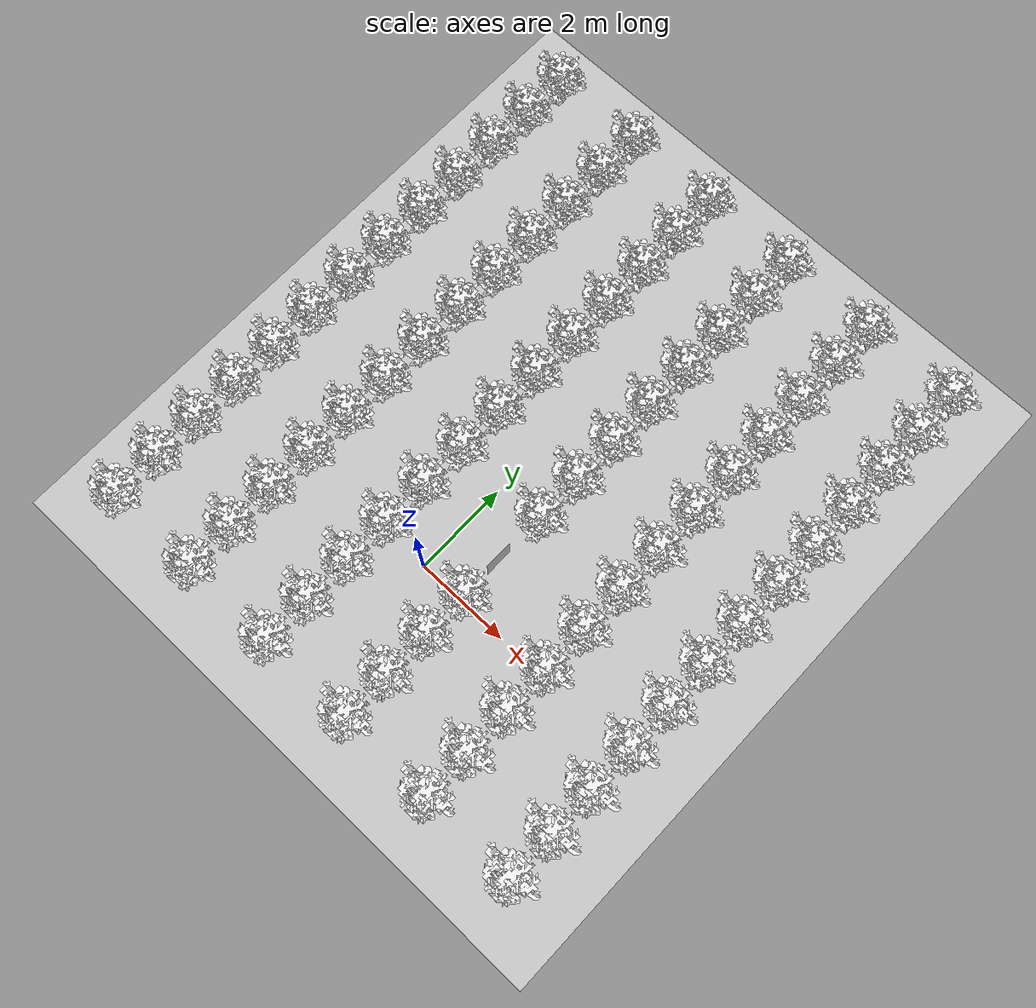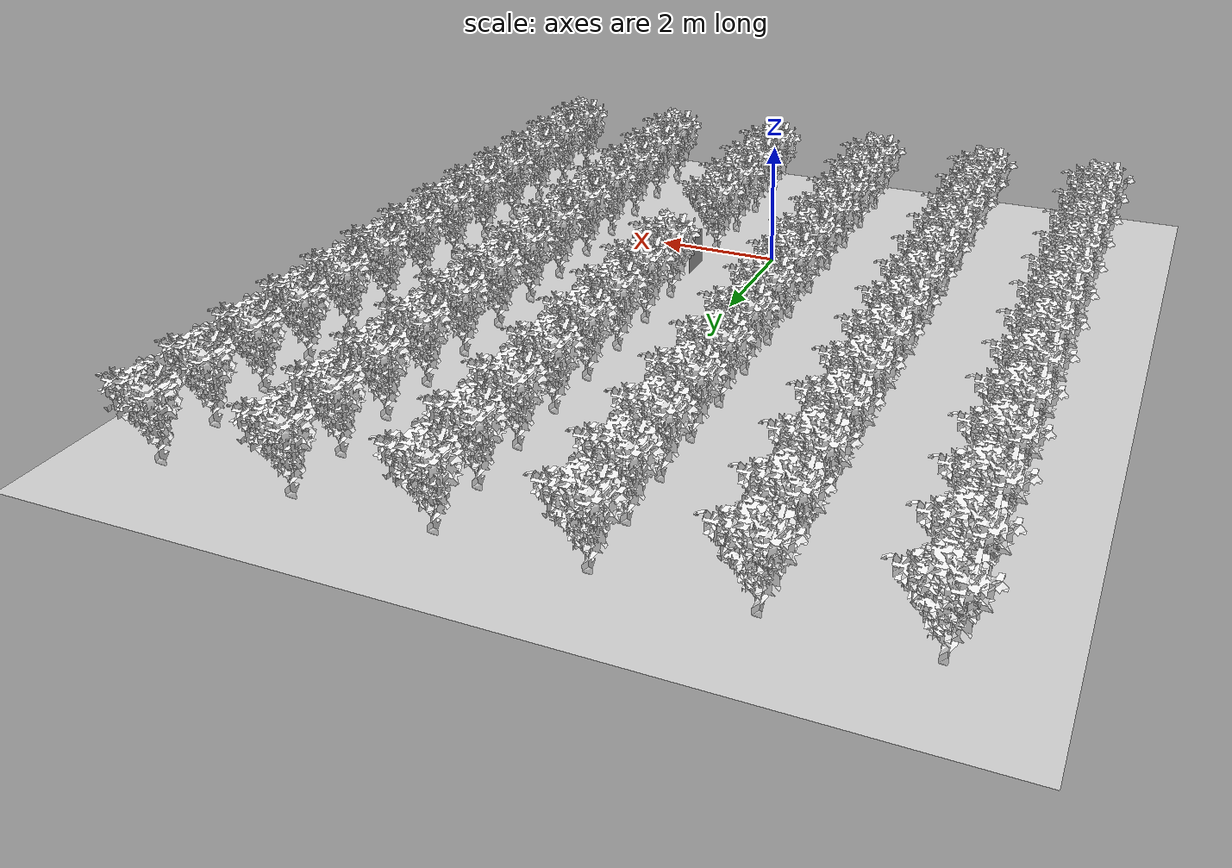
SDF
<?xml version="1.0" ?>
  <sdf version="1.7">
  <world name="default">
  <physics type="ode">
      <ode>
        <solver>
          <type>world</type>
        </solver>
        <constraints>
          <contact_max_correcting_vel>0.1</contact_max_correcting_vel>
          <contact_surface_layer>0.0001</contact_surface_layer>
        </constraints>
      </ode>
      <max_step_size>0.01</max_step_size>
      <real_time_factor>0.8</real_time_factor>
      <real_time_update_rate>100</real_time_update_rate>
    </physics>
    <gravity>0.0 0.0 -9.81</gravity>
  <!-- A global light source -->
    <include>
      <uri>model://sun</uri>
    </include>
    <gui fullscreen='0'>
      <camera name='user_camera'>
        <pose>-0.059361 2.171367 15.466796 -0.000711 1.569796 1.571162</pose>
        <view_controller>orbit</view_controller>
        <projection_type>perspective</projection_type>
      </camera>
    </gui>

    <model name='tree_0'>
    <static>true</static>
    <link name='link'>
      <visual name='trunk'>
        <geometry>
          <mesh>
            <uri>model://meshes/Tree_1_Trunk.dae</uri>
          </mesh>
        </geometry>
        <material>
          <script>
            <uri>model://materials/scripts/</uri>
            <uri>model://materials/textures/</uri>
            <name>Vine/Bark</name>
          </script>
        </material>
      </visual>
      <visual name='leafa'>
        <geometry>
          <mesh>
            <uri>model://meshes/Tree_1_Leaf_1.dae</uri>
          </mesh>
        </geometry>
        <material>
          <script>
            <uri>model://materials/scripts/</uri>
            <uri>model://materials/textures/</uri>
            <name>Vine/Leafa</name>
          </script>
        </material>
      </visual>
      <visual name='leafb'>
        <geometry>
          <mesh>
            <uri>model://meshes/Tree_1_Leaf_2.dae</uri>
          </mesh>
        </geometry>
        <material>
          <script>
            <uri>model://materials/scripts/</uri>
            <uri>model://materials/textures/</uri>
            <name>Vine/Leafb</name>
          </script>
        </material>
      </visual>
      <visual name='leafc'>
        <geometry>
          <mesh>
            <uri>model://meshes/Tree_1_Leaf_3.dae</uri>
          </mesh>
        </geometry>
        <material>
          <script>
            <uri>model://materials/scripts/</uri>
            <uri>model://materials/textures/</uri>
            <name>Vine/Leafc</name>
          </script>
        </material>
      </visual>
      <self_collide>0</self_collide>
      <enable_wind>0</enable_wind>
      <kinematic>0</kinematic>
    </link>
    <pose>-5 -3 -0.3 0 0 0</pose>
  </model>

    <model name='tree_1'>
    <static>true</static>
    <link name='link'>
      <visual name='trunk'>
        <geometry>
          <mesh>
            <uri>model://meshes/Tree_1_Trunk.dae</uri>
          </mesh>
        </geometry>
        <material>
          <script>
            <uri>model://materials/scripts/</uri>
            <uri>model://materials/textures/</uri>
            <name>Vine/Bark</name>
          </script>
        </material>
      </visual>
      <visual name='leafa'>
        <geometry>
          <mesh>
            <uri>model://meshes/Tree_1_Leaf_1.dae</uri>
          </mesh>
        </geometry>
        <material>
          <script>
            <uri>model://materials/scripts/</uri>
            <uri>model://materials/textures/</uri>
            <name>Vine/Leafa</name>
          </script>
        </material>
      </visual>
      <visual name='leafb'>
        <geometry>
          <mesh>
            <uri>model://meshes/Tree_1_Leaf_2.dae</uri>
          </mesh>
        </geometry>
        <material>
          <script>
            <uri>model://materials/scripts/</uri>
            <uri>model://materials/textures/</uri>
            <name>Vine/Leafb</name>
          </script>
        </material>
      </visual>
      <visual name='leafc'>
        <geometry>
          <mesh>
            <uri>model://meshes/Tree_1_Leaf_3.dae</uri>
          </mesh>
        </geometry>
        <material>
          <script>
            <uri>model://materials/scripts/</uri>
            <uri>model://materials/textures/</uri>
            <name>Vine/Leafc</name>
          </script>
        </material>
      </visual>
      <self_collide>0</self_collide>
      <enable_wind>0</enable_wind>
      <kinematic>0</kinematic>
    </link>
    <pose>-5 -2 -0.3 0 0 0</pose>
  </model>

    <model name='tree_2'>
    <static>true</static>
    <link name='link'>
      <visual name='trunk'>
        <geometry>
          <mesh>
            <uri>model://meshes/Tree_1_Trunk.dae</uri>
          </mesh>
        </geometry>
        <material>
          <script>
            <uri>model://materials/scripts/</uri>
            <uri>model://materials/textures/</uri>
            <name>Vine/Bark</name>
          </script>
        </material>
      </visual>
      <visual name='leafa'>
        <geometry>
          <mesh>
            <uri>model://meshes/Tree_1_Leaf_1.dae</uri>
          </mesh>
        </geometry>
        <material>
          <script>
            <uri>model://materials/scripts/</uri>
            <uri>model://materials/textures/</uri>
            <name>Vine/Leafa</name>
          </script>
        </material>
      </visual>
      <visual name='leafb'>
        <geometry>
          <mesh>
            <uri>model://meshes/Tree_1_Leaf_2.dae</uri>
          </mesh>
        </geometry>
        <material>
          <script>
            <uri>model://materials/scripts/</uri>
            <uri>model://materials/textures/</uri>
            <name>Vine/Leafb</name>
          </script>
        </material>
      </visual>
      <visual name='leafc'>
        <geometry>
          <mesh>
            <uri>model://meshes/Tree_1_Leaf_3.dae</uri>
          </mesh>
        </geometry>
        <material>
          <script>
            <uri>model://materials/scripts/</uri>
            <uri>model://materials/textures/</uri>
            <name>Vine/Leafc</name>
          </script>
        </material>
      </visual>
      <self_collide>0</self_collide>
      <enable_wind>0</enable_wind>
      <kinematic>0</kinematic>
    </link>
    <pose>-5 -1 -0.3 0 0 0</pose>
  </model>

    <model name='tree_3'>
    <static>true</static>
    <link name='link'>
      <visual name='trunk'>
        <geometry>
          <mesh>
            <uri>model://meshes/Tree_1_Trunk.dae</uri>
          </mesh>
        </geometry>
        <material>
          <script>
            <uri>model://materials/scripts/</uri>
            <uri>model://materials/textures/</uri>
            <name>Vine/Bark</name>
          </script>
        </material>
      </visual>
      <visual name='leafa'>
        <geometry>
          <mesh>
            <uri>model://meshes/Tree_1_Leaf_1.dae</uri>
          </mesh>
        </geometry>
        <material>
          <script>
            <uri>model://materials/scripts/</uri>
            <uri>model://materials/textures/</uri>
            <name>Vine/Leafa</name>
          </script>
        </material>
      </visual>
      <visual name='leafb'>
        <geometry>
          <mesh>
            <uri>model://meshes/Tree_1_Leaf_2.dae</uri>
          </mesh>
        </geometry>
        <material>
          <script>
            <uri>model://materials/scripts/</uri>
            <uri>model://materials/textures/</uri>
            <name>Vine/Leafb</name>
          </script>
        </material>
      </visual>
      <visual name='leafc'>
        <geometry>
          <mesh>
            <uri>model://meshes/Tree_1_Leaf_3.dae</uri>
          </mesh>
        </geometry>
        <material>
          <script>
            <uri>model://materials/scripts/</uri>
            <uri>model://materials/textures/</uri>
            <name>Vine/Leafc</name>
          </script>
        </material>
      </visual>
      <self_collide>0</self_collide>
      <enable_wind>0</enable_wind>
      <kinematic>0</kinematic>
    </link>
    <pose>-5 0 -0.3 0 0 0</pose>
  </model>

    <model name='tree_4'>
    <static>true</static>
    <link name='link'>
      <visual name='trunk'>
        <geometry>
          <mesh>
            <uri>model://meshes/Tree_1_Trunk.dae</uri>
          </mesh>
        </geometry>
        <material>
          <script>
            <uri>model://materials/scripts/</uri>
            <uri>model://materials/textures/</uri>
            <name>Vine/Bark</name>
          </script>
        </material>
      </visual>
      <visual name='leafa'>
        <geometry>
          <mesh>
            <uri>model://meshes/Tree_1_Leaf_1.dae</uri>
          </mesh>
        </geometry>
        <material>
          <script>
            <uri>model://materials/scripts/</uri>
            <uri>model://materials/textures/</uri>
            <name>Vine/Leafa</name>
          </script>
        </material>
      </visual>
      <visual name='leafb'>
        <geometry>
          <mesh>
            <uri>model://meshes/Tree_1_Leaf_2.dae</uri>
          </mesh>
        </geometry>
        <material>
          <script>
            <uri>model://materials/scripts/</uri>
            <uri>model://materials/textures/</uri>
            <name>Vine/Leafb</name>
          </script>
        </material>
      </visual>
      <visual name='leafc'>
        <geometry>
          <mesh>
            <uri>model://meshes/Tree_1_Leaf_3.dae</uri>
          </mesh>
        </geometry>
        <material>
          <script>
            <uri>model://materials/scripts/</uri>
            <uri>model://materials/textures/</uri>
            <name>Vine/Leafc</name>
          </script>
        </material>
      </visual>
      <self_collide>0</self_collide>
      <enable_wind>0</enable_wind>
      <kinematic>0</kinematic>
    </link>
    <pose>-5 1 -0.3 0 0 0</pose>
  </model>

    <model name='tree_5'>
    <static>true</static>
    <link name='link'>
      <visual name='trunk'>
        <geometry>
          <mesh>
            <uri>model://meshes/Tree_1_Trunk.dae</uri>
          </mesh>
        </geometry>
        <material>
          <script>
            <uri>model://materials/scripts/</uri>
            <uri>model://materials/textures/</uri>
            <name>Vine/Bark</name>
          </script>
        </material>
      </visual>
      <visual name='leafa'>
        <geometry>
          <mesh>
            <uri>model://meshes/Tree_1_Leaf_1.dae</uri>
          </mesh>
        </geometry>
        <material>
          <script>
            <uri>model://materials/scripts/</uri>
            <uri>model://materials/textures/</uri>
            <name>Vine/Leafa</name>
          </script>
        </material>
      </visual>
      <visual name='leafb'>
        <geometry>
          <mesh>
            <uri>model://meshes/Tree_1_Leaf_2.dae</uri>
          </mesh>
        </geometry>
        <material>
          <script>
            <uri>model://materials/scripts/</uri>
            <uri>model://materials/textures/</uri>
            <name>Vine/Leafb</name>
          </script>
        </material>
      </visual>
      <visual name='leafc'>
        <geometry>
          <mesh>
            <uri>model://meshes/Tree_1_Leaf_3.dae</uri>
          </mesh>
        </geometry>
        <material>
          <script>
            <uri>model://materials/scripts/</uri>
            <uri>model://materials/textures/</uri>
            <name>Vine/Leafc</name>
          </script>
        </material>
      </visual>
      <self_collide>0</self_collide>
      <enable_wind>0</enable_wind>
      <kinematic>0</kinematic>
    </link>
    <pose>-5 2 -0.3 0 0 0</pose>
  </model>

    <model name='tree_6'>
    <static>true</static>
    <link name='link'>
      <visual name='trunk'>
        <geometry>
          <mesh>
            <uri>model://meshes/Tree_1_Trunk.dae</uri>
          </mesh>
        </geometry>
        <material>
          <script>
            <uri>model://materials/scripts/</uri>
            <uri>model://materials/textures/</uri>
            <name>Vine/Bark</name>
          </script>
        </material>
      </visual>
      <visual name='leafa'>
        <geometry>
          <mesh>
            <uri>model://meshes/Tree_1_Leaf_1.dae</uri>
          </mesh>
        </geometry>
        <material>
          <script>
            <uri>model://materials/scripts/</uri>
            <uri>model://materials/textures/</uri>
            <name>Vine/Leafa</name>
          </script>
        </material>
      </visual>
      <visual name='leafb'>
        <geometry>
          <mesh>
            <uri>model://meshes/Tree_1_Leaf_2.dae</uri>
          </mesh>
        </geometry>
        <material>
          <script>
            <uri>model://materials/scripts/</uri>
            <uri>model://materials/textures/</uri>
            <name>Vine/Leafb</name>
          </script>
        </material>
      </visual>
      <visual name='leafc'>
        <geometry>
          <mesh>
            <uri>model://meshes/Tree_1_Leaf_3.dae</uri>
          </mesh>
        </geometry>
        <material>
          <script>
            <uri>model://materials/scripts/</uri>
            <uri>model://materials/textures/</uri>
            <name>Vine/Leafc</name>
          </script>
        </material>
      </visual>
      <self_collide>0</self_collide>
      <enable_wind>0</enable_wind>
      <kinematic>0</kinematic>
    </link>
    <pose>-5 3 -0.3 0 0 0</pose>
  </model>

    <model name='tree_7'>
    <static>true</static>
    <link name='link'>
      <visual name='trunk'>
        <geometry>
          <mesh>
            <uri>model://meshes/Tree_1_Trunk.dae</uri>
          </mesh>
        </geometry>
        <material>
          <script>
            <uri>model://materials/scripts/</uri>
            <uri>model://materials/textures/</uri>
            <name>Vine/Bark</name>
          </script>
        </material>
      </visual>
      <visual name='leafa'>
        <geometry>
          <mesh>
            <uri>model://meshes/Tree_1_Leaf_1.dae</uri>
          </mesh>
        </geometry>
        <material>
          <script>
            <uri>model://materials/scripts/</uri>
            <uri>model://materials/textures/</uri>
            <name>Vine/Leafa</name>
          </script>
        </material>
      </visual>
      <visual name='leafb'>
        <geometry>
          <mesh>
            <uri>model://meshes/Tree_1_Leaf_2.dae</uri>
          </mesh>
        </geometry>
        <material>
          <script>
            <uri>model://materials/scripts/</uri>
            <uri>model://materials/textures/</uri>
            <name>Vine/Leafb</name>
          </script>
        </material>
      </visual>
      <visual name='leafc'>
        <geometry>
          <mesh>
            <uri>model://meshes/Tree_1_Leaf_3.dae</uri>
          </mesh>
        </geometry>
        <material>
          <script>
            <uri>model://materials/scripts/</uri>
            <uri>model://materials/textures/</uri>
            <name>Vine/Leafc</name>
          </script>
        </material>
      </visual>
      <self_collide>0</self_collide>
      <enable_wind>0</enable_wind>
      <kinematic>0</kinematic>
    </link>
    <pose>-5 4 -0.3 0 0 0</pose>
  </model>

    <model name='tree_8'>
    <static>true</static>
    <link name='link'>
      <visual name='trunk'>
        <geometry>
          <mesh>
            <uri>model://meshes/Tree_1_Trunk.dae</uri>
          </mesh>
        </geometry>
        <material>
          <script>
            <uri>model://materials/scripts/</uri>
            <uri>model://materials/textures/</uri>
            <name>Vine/Bark</name>
          </script>
        </material>
      </visual>
      <visual name='leafa'>
        <geometry>
          <mesh>
            <uri>model://meshes/Tree_1_Leaf_1.dae</uri>
          </mesh>
        </geometry>
        <material>
          <script>
            <uri>model://materials/scripts/</uri>
            <uri>model://materials/textures/</uri>
            <name>Vine/Leafa</name>
          </script>
        </material>
      </visual>
      <visual name='leafb'>
        <geometry>
          <mesh>
            <uri>model://meshes/Tree_1_Leaf_2.dae</uri>
          </mesh>
        </geometry>
        <material>
          <script>
            <uri>model://materials/scripts/</uri>
            <uri>model://materials/textures/</uri>
            <name>Vine/Leafb</name>
          </script>
        </material>
      </visual>
      <visual name='leafc'>
        <geometry>
          <mesh>
            <uri>model://meshes/Tree_1_Leaf_3.dae</uri>
          </mesh>
        </geometry>
        <material>
          <script>
            <uri>model://materials/scripts/</uri>
            <uri>model://materials/textures/</uri>
            <name>Vine/Leafc</name>
          </script>
        </material>
      </visual>
      <self_collide>0</self_collide>
      <enable_wind>0</enable_wind>
      <kinematic>0</kinematic>
    </link>
    <pose>-5 5 -0.3 0 0 0</pose>
  </model>

    <model name='tree_9'>
    <static>true</static>
    <link name='link'>
      <visual name='trunk'>
        <geometry>
          <mesh>
            <uri>model://meshes/Tree_1_Trunk.dae</uri>
          </mesh>
        </geometry>
        <material>
          <script>
            <uri>model://materials/scripts/</uri>
            <uri>model://materials/textures/</uri>
            <name>Vine/Bark</name>
          </script>
        </material>
      </visual>
      <visual name='leafa'>
        <geometry>
          <mesh>
            <uri>model://meshes/Tree_1_Leaf_1.dae</uri>
          </mesh>
        </geometry>
        <material>
          <script>
            <uri>model://materials/scripts/</uri>
            <uri>model://materials/textures/</uri>
            <name>Vine/Leafa</name>
          </script>
        </material>
      </visual>
      <visual name='leafb'>
        <geometry>
          <mesh>
            <uri>model://meshes/Tree_1_Leaf_2.dae</uri>
          </mesh>
        </geometry>
        <material>
          <script>
            <uri>model://materials/scripts/</uri>
            <uri>model://materials/textures/</uri>
            <name>Vine/Leafb</name>
          </script>
        </material>
      </visual>
      <visual name='leafc'>
        <geometry>
          <mesh>
            <uri>model://meshes/Tree_1_Leaf_3.dae</uri>
          </mesh>
        </geometry>
        <material>
          <script>
            <uri>model://materials/scripts/</uri>
            <uri>model://materials/textures/</uri>
            <name>Vine/Leafc</name>
          </script>
        </material>
      </visual>
      <self_collide>0</self_collide>
      <enable_wind>0</enable_wind>
      <kinematic>0</kinematic>
    </link>
    <pose>-5 6 -0.3 0 0 0</pose>
  </model>

    <model name='tree_10'>
    <static>true</static>
    <link name='link'>
      <visual name='trunk'>
        <geometry>
          <mesh>
            <uri>model://meshes/Tree_1_Trunk.dae</uri>
          </mesh>
        </geometry>
        <material>
          <script>
            <uri>model://materials/scripts/</uri>
            <uri>model://materials/textures/</uri>
            <name>Vine/Bark</name>
          </script>
        </material>
      </visual>
      <visual name='leafa'>
        <geometry>
          <mesh>
            <uri>model://meshes/Tree_1_Leaf_1.dae</uri>
          </mesh>
        </geometry>
        <material>
          <script>
            <uri>model://materials/scripts/</uri>
            <uri>model://materials/textures/</uri>
            <name>Vine/Leafa</name>
          </script>
        </material>
      </visual>
      <visual name='leafb'>
        <geometry>
          <mesh>
            <uri>model://meshes/Tree_1_Leaf_2.dae</uri>
          </mesh>
        </geometry>
        <material>
          <script>
            <uri>model://materials/scripts/</uri>
            <uri>model://materials/textures/</uri>
            <name>Vine/Leafb</name>
          </script>
        </material>
      </visual>
      <visual name='leafc'>
        <geometry>
          <mesh>
            <uri>model://meshes/Tree_1_Leaf_3.dae</uri>
          </mesh>
        </geometry>
        <material>
          <script>
            <uri>model://materials/scripts/</uri>
            <uri>model://materials/textures/</uri>
            <name>Vine/Leafc</name>
          </script>
        </material>
      </visual>
      <self_collide>0</self_collide>
      <enable_wind>0</enable_wind>
      <kinematic>0</kinematic>
    </link>
    <pose>-5 7 -0.3 0 0 0</pose>
  </model>

    <model name='tree_11'>
    <static>true</static>
    <link name='link'>
      <visual name='trunk'>
        <geometry>
          <mesh>
            <uri>model://meshes/Tree_1_Trunk.dae</uri>
          </mesh>
        </geometry>
        <material>
          <script>
            <uri>model://materials/scripts/</uri>
            <uri>model://materials/textures/</uri>
            <name>Vine/Bark</name>
          </script>
        </material>
      </visual>
      <visual name='leafa'>
        <geometry>
          <mesh>
            <uri>model://meshes/Tree_1_Leaf_1.dae</uri>
          </mesh>
        </geometry>
        <material>
          <script>
            <uri>model://materials/scripts/</uri>
            <uri>model://materials/textures/</uri>
            <name>Vine/Leafa</name>
          </script>
        </material>
      </visual>
      <visual name='leafb'>
        <geometry>
          <mesh>
            <uri>model://meshes/Tree_1_Leaf_2.dae</uri>
          </mesh>
        </geometry>
        <material>
          <script>
            <uri>model://materials/scripts/</uri>
            <uri>model://materials/textures/</uri>
            <name>Vine/Leafb</name>
          </script>
        </material>
      </visual>
      <visual name='leafc'>
        <geometry>
          <mesh>
            <uri>model://meshes/Tree_1_Leaf_3.dae</uri>
          </mesh>
        </geometry>
        <material>
          <script>
            <uri>model://materials/scripts/</uri>
            <uri>model://materials/textures/</uri>
            <name>Vine/Leafc</name>
          </script>
        </material>
      </visual>
      <self_collide>0</self_collide>
      <enable_wind>0</enable_wind>
      <kinematic>0</kinematic>
    </link>
    <pose>-5 8 -0.3 0 0 0</pose>
  </model>

    <model name='tree_12'>
    <static>true</static>
    <link name='link'>
      <visual name='trunk'>
        <geometry>
          <mesh>
            <uri>model://meshes/Tree_1_Trunk.dae</uri>
          </mesh>
        </geometry>
        <material>
          <script>
            <uri>model://materials/scripts/</uri>
            <uri>model://materials/textures/</uri>
            <name>Vine/Bark</name>
          </script>
        </material>
      </visual>
      <visual name='leafa'>
        <geometry>
          <mesh>
            <uri>model://meshes/Tree_1_Leaf_1.dae</uri>
          </mesh>
        </geometry>
        <material>
          <script>
            <uri>model://materials/scripts/</uri>
            <uri>model://materials/textures/</uri>
            <name>Vine/Leafa</name>
          </script>
        </material>
      </visual>
      <visual name='leafb'>
        <geometry>
          <mesh>
            <uri>model://meshes/Tree_1_Leaf_2.dae</uri>
          </mesh>
        </geometry>
        <material>
          <script>
            <uri>model://materials/scripts/</uri>
            <uri>model://materials/textures/</uri>
            <name>Vine/Leafb</name>
          </script>
        </material>
      </visual>
      <visual name='leafc'>
        <geometry>
          <mesh>
            <uri>model://meshes/Tree_1_Leaf_3.dae</uri>
          </mesh>
        </geometry>
        <material>
          <script>
            <uri>model://materials/scripts/</uri>
            <uri>model://materials/textures/</uri>
            <name>Vine/Leafc</name>
          </script>
        </material>
      </visual>
      <self_collide>0</self_collide>
      <enable_wind>0</enable_wind>
      <kinematic>0</kinematic>
    </link>
    <pose>-5 9 -0.3 0 0 0</pose>
  </model>

    <model name='tree_13'>
    <static>true</static>
    <link name='link'>
      <visual name='trunk'>
        <geometry>
          <mesh>
            <uri>model://meshes/Tree_1_Trunk.dae</uri>
          </mesh>
        </geometry>
        <material>
          <script>
            <uri>model://materials/scripts/</uri>
            <uri>model://materials/textures/</uri>
            <name>Vine/Bark</name>
          </script>
        </material>
      </visual>
      <visual name='leafa'>
        <geometry>
          <mesh>
            <uri>model://meshes/Tree_1_Leaf_1.dae</uri>
          </mesh>
        </geometry>
        <material>
          <script>
            <uri>model://materials/scripts/</uri>
            <uri>model://materials/textures/</uri>
            <name>Vine/Leafa</name>
          </script>
        </material>
      </visual>
      <visual name='leafb'>
        <geometry>
          <mesh>
            <uri>model://meshes/Tree_1_Leaf_2.dae</uri>
          </mesh>
        </geometry>
        <material>
          <script>
            <uri>model://materials/scripts/</uri>
            <uri>model://materials/textures/</uri>
            <name>Vine/Leafb</name>
          </script>
        </material>
      </visual>
      <visual name='leafc'>
        <geometry>
          <mesh>
            <uri>model://meshes/Tree_1_Leaf_3.dae</uri>
          </mesh>
        </geometry>
        <material>
          <script>
            <uri>model://materials/scripts/</uri>
            <uri>model://materials/textures/</uri>
            <name>Vine/Leafc</name>
          </script>
        </material>
      </visual>
      <self_collide>0</self_collide>
      <enable_wind>0</enable_wind>
      <kinematic>0</kinematic>
    </link>
    <pose>-3 -3 -0.3 0 0 0</pose>
  </model>

    <model name='tree_14'>
    <static>true</static>
    <link name='link'>
      <visual name='trunk'>
        <geometry>
          <mesh>
            <uri>model://meshes/Tree_1_Trunk.dae</uri>
          </mesh>
        </geometry>
        <material>
          <script>
            <uri>model://materials/scripts/</uri>
            <uri>model://materials/textures/</uri>
            <name>Vine/Bark</name>
          </script>
        </material>
      </visual>
      <visual name='leafa'>
        <geometry>
          <mesh>
            <uri>model://meshes/Tree_1_Leaf_1.dae</uri>
          </mesh>
        </geometry>
        <material>
          <script>
            <uri>model://materials/scripts/</uri>
            <uri>model://materials/textures/</uri>
            <name>Vine/Leafa</name>
          </script>
        </material>
      </visual>
      <visual name='leafb'>
        <geometry>
          <mesh>
            <uri>model://meshes/Tree_1_Leaf_2.dae</uri>
          </mesh>
        </geometry>
        <material>
          <script>
            <uri>model://materials/scripts/</uri>
            <uri>model://materials/textures/</uri>
            <name>Vine/Leafb</name>
          </script>
        </material>
      </visual>
      <visual name='leafc'>
        <geometry>
          <mesh>
            <uri>model://meshes/Tree_1_Leaf_3.dae</uri>
          </mesh>
        </geometry>
        <material>
          <script>
            <uri>model://materials/scripts/</uri>
            <uri>model://materials/textures/</uri>
            <name>Vine/Leafc</name>
          </script>
        </material>
      </visual>
      <self_collide>0</self_collide>
      <enable_wind>0</enable_wind>
      <kinematic>0</kinematic>
    </link>
    <pose>-3 -2 -0.3 0 0 0</pose>
  </model>

    <model name='tree_15'>
    <static>true</static>
    <link name='link'>
      <visual name='trunk'>
        <geometry>
          <mesh>
            <uri>model://meshes/Tree_1_Trunk.dae</uri>
          </mesh>
        </geometry>
        <material>
          <script>
            <uri>model://materials/scripts/</uri>
            <uri>model://materials/textures/</uri>
            <name>Vine/Bark</name>
          </script>
        </material>
      </visual>
      <visual name='leafa'>
        <geometry>
          <mesh>
            <uri>model://meshes/Tree_1_Leaf_1.dae</uri>
          </mesh>
        </geometry>
        <material>
          <script>
            <uri>model://materials/scripts/</uri>
            <uri>model://materials/textures/</uri>
            <name>Vine/Leafa</name>
          </script>
        </material>
      </visual>
      <visual name='leafb'>
        <geometry>
          <mesh>
            <uri>model://meshes/Tree_1_Leaf_2.dae</uri>
          </mesh>
        </geometry>
        <material>
          <script>
            <uri>model://materials/scripts/</uri>
            <uri>model://materials/textures/</uri>
            <name>Vine/Leafb</name>
          </script>
        </material>
      </visual>
      <visual name='leafc'>
        <geometry>
          <mesh>
            <uri>model://meshes/Tree_1_Leaf_3.dae</uri>
          </mesh>
        </geometry>
        <material>
          <script>
            <uri>model://materials/scripts/</uri>
            <uri>model://materials/textures/</uri>
            <name>Vine/Leafc</name>
          </script>
        </material>
      </visual>
      <self_collide>0</self_collide>
      <enable_wind>0</enable_wind>
      <kinematic>0</kinematic>
    </link>
    <pose>-3 -1 -0.3 0 0 0</pose>
  </model>

    <model name='tree_16'>
    <static>true</static>
    <link name='link'>
      <visual name='trunk'>
        <geometry>
          <mesh>
            <uri>model://meshes/Tree_1_Trunk.dae</uri>
          </mesh>
        </geometry>
        <material>
          <script>
            <uri>model://materials/scripts/</uri>
            <uri>model://materials/textures/</uri>
            <name>Vine/Bark</name>
          </script>
        </material>
      </visual>
      <visual name='leafa'>
        <geometry>
          <mesh>
            <uri>model://meshes/Tree_1_Leaf_1.dae</uri>
          </mesh>
        </geometry>
        <material>
          <script>
            <uri>model://materials/scripts/</uri>
            <uri>model://materials/textures/</uri>
            <name>Vine/Leafa</name>
          </script>
        </material>
      </visual>
      <visual name='leafb'>
        <geometry>
          <mesh>
            <uri>model://meshes/Tree_1_Leaf_2.dae</uri>
          </mesh>
        </geometry>
        <material>
          <script>
            <uri>model://materials/scripts/</uri>
            <uri>model://materials/textures/</uri>
            <name>Vine/Leafb</name>
          </script>
        </material>
      </visual>
      <visual name='leafc'>
        <geometry>
          <mesh>
            <uri>model://meshes/Tree_1_Leaf_3.dae</uri>
          </mesh>
        </geometry>
        <material>
          <script>
            <uri>model://materials/scripts/</uri>
            <uri>model://materials/textures/</uri>
            <name>Vine/Leafc</name>
          </script>
        </material>
      </visual>
      <self_collide>0</self_collide>
      <enable_wind>0</enable_wind>
      <kinematic>0</kinematic>
    </link>
    <pose>-3 0 -0.3 0 0 0</pose>
  </model>

    <model name='tree_17'>
    <static>true</static>
    <link name='link'>
      <visual name='trunk'>
        <geometry>
          <mesh>
            <uri>model://meshes/Tree_1_Trunk.dae</uri>
          </mesh>
        </geometry>
        <material>
          <script>
            <uri>model://materials/scripts/</uri>
            <uri>model://materials/textures/</uri>
            <name>Vine/Bark</name>
          </script>
        </material>
      </visual>
      <visual name='leafa'>
        <geometry>
          <mesh>
            <uri>model://meshes/Tree_1_Leaf_1.dae</uri>
          </mesh>
        </geometry>
        <material>
          <script>
            <uri>model://materials/scripts/</uri>
            <uri>model://materials/textures/</uri>
            <name>Vine/Leafa</name>
          </script>
        </material>
      </visual>
      <visual name='leafb'>
        <geometry>
          <mesh>
            <uri>model://meshes/Tree_1_Leaf_2.dae</uri>
          </mesh>
        </geometry>
        <material>
          <script>
            <uri>model://materials/scripts/</uri>
            <uri>model://materials/textures/</uri>
            <name>Vine/Leafb</name>
          </script>
        </material>
      </visual>
      <visual name='leafc'>
        <geometry>
          <mesh>
            <uri>model://meshes/Tree_1_Leaf_3.dae</uri>
          </mesh>
        </geometry>
        <material>
          <script>
            <uri>model://materials/scripts/</uri>
            <uri>model://materials/textures/</uri>
            <name>Vine/Leafc</name>
          </script>
        </material>
      </visual>
      <self_collide>0</self_collide>
      <enable_wind>0</enable_wind>
      <kinematic>0</kinematic>
    </link>
    <pose>-3 1 -0.3 0 0 0</pose>
  </model>

    <model name='tree_18'>
    <static>true</static>
    <link name='link'>
      <visual name='trunk'>
        <geometry>
          <mesh>
            <uri>model://meshes/Tree_1_Trunk.dae</uri>
          </mesh>
        </geometry>
        <material>
          <script>
            <uri>model://materials/scripts/</uri>
            <uri>model://materials/textures/</uri>
            <name>Vine/Bark</name>
          </script>
        </material>
      </visual>
      <visual name='leafa'>
        <geometry>
          <mesh>
            <uri>model://meshes/Tree_1_Leaf_1.dae</uri>
          </mesh>
        </geometry>
        <material>
          <script>
            <uri>model://materials/scripts/</uri>
            <uri>model://materials/textures/</uri>
            <name>Vine/Leafa</name>
          </script>
        </material>
      </visual>
      <visual name='leafb'>
        <geometry>
          <mesh>
            <uri>model://meshes/Tree_1_Leaf_2.dae</uri>
          </mesh>
        </geometry>
        <material>
          <script>
            <uri>model://materials/scripts/</uri>
            <uri>model://materials/textures/</uri>
            <name>Vine/Leafb</name>
          </script>
        </material>
      </visual>
      <visual name='leafc'>
        <geometry>
          <mesh>
            <uri>model://meshes/Tree_1_Leaf_3.dae</uri>
          </mesh>
        </geometry>
        <material>
          <script>
            <uri>model://materials/scripts/</uri>
            <uri>model://materials/textures/</uri>
            <name>Vine/Leafc</name>
          </script>
        </material>
      </visual>
      <self_collide>0</self_collide>
      <enable_wind>0</enable_wind>
      <kinematic>0</kinematic>
    </link>
    <pose>-3 2 -0.3 0 0 0</pose>
  </model>

    <model name='tree_19'>
    <static>true</static>
    <link name='link'>
      <visual name='trunk'>
        <geometry>
          <mesh>
            <uri>model://meshes/Tree_1_Trunk.dae</uri>
          </mesh>
        </geometry>
        <material>
          <script>
            <uri>model://materials/scripts/</uri>
            <uri>model://materials/textures/</uri>
            <name>Vine/Bark</name>
          </script>
        </material>
      </visual>
      <visual name='leafa'>
        <geometry>
          <mesh>
            <uri>model://meshes/Tree_1_Leaf_1.dae</uri>
          </mesh>
        </geometry>
        <material>
          <script>
            <uri>model://materials/scripts/</uri>
            <uri>model://materials/textures/</uri>
            <name>Vine/Leafa</name>
          </script>
        </material>
      </visual>
      <visual name='leafb'>
        <geometry>
          <mesh>
            <uri>model://meshes/Tree_1_Leaf_2.dae</uri>
          </mesh>
        </geometry>
        <material>
          <script>
            <uri>model://materials/scripts/</uri>
            <uri>model://materials/textures/</uri>
            <name>Vine/Leafb</name>
          </script>
        </material>
      </visual>
      <visual name='leafc'>
        <geometry>
          <mesh>
            <uri>model://meshes/Tree_1_Leaf_3.dae</uri>
          </mesh>
        </geometry>
        <material>
          <script>
            <uri>model://materials/scripts/</uri>
            <uri>model://materials/textures/</uri>
            <name>Vine/Leafc</name>
          </script>
        </material>
      </visual>
      <self_collide>0</self_collide>
      <enable_wind>0</enable_wind>
      <kinematic>0</kinematic>
    </link>
    <pose>-3 3 -0.3 0 0 0</pose>
  </model>

    <model name='tree_20'>
    <static>true</static>
    <link name='link'>
      <visual name='trunk'>
        <geometry>
          <mesh>
            <uri>model://meshes/Tree_1_Trunk.dae</uri>
          </mesh>
        </geometry>
        <material>
          <script>
            <uri>model://materials/scripts/</uri>
            <uri>model://materials/textures/</uri>
            <name>Vine/Bark</name>
          </script>
        </material>
      </visual>
      <visual name='leafa'>
        <geometry>
          <mesh>
            <uri>model://meshes/Tree_1_Leaf_1.dae</uri>
          </mesh>
        </geometry>
        <material>
          <script>
            <uri>model://materials/scripts/</uri>
            <uri>model://materials/textures/</uri>
            <name>Vine/Leafa</name>
          </script>
        </material>
      </visual>
      <visual name='leafb'>
        <geometry>
          <mesh>
            <uri>model://meshes/Tree_1_Leaf_2.dae</uri>
          </mesh>
        </geometry>
        <material>
          <script>
            <uri>model://materials/scripts/</uri>
            <uri>model://materials/textures/</uri>
            <name>Vine/Leafb</name>
          </script>
        </material>
      </visual>
      <visual name='leafc'>
        <geometry>
          <mesh>
            <uri>model://meshes/Tree_1_Leaf_3.dae</uri>
          </mesh>
        </geometry>
        <material>
          <script>
            <uri>model://materials/scripts/</uri>
            <uri>model://materials/textures/</uri>
            <name>Vine/Leafc</name>
          </script>
        </material>
      </visual>
      <self_collide>0</self_collide>
      <enable_wind>0</enable_wind>
      <kinematic>0</kinematic>
    </link>
    <pose>-3 4 -0.3 0 0 0</pose>
  </model>

    <model name='tree_21'>
    <static>true</static>
    <link name='link'>
      <visual name='trunk'>
        <geometry>
          <mesh>
            <uri>model://meshes/Tree_1_Trunk.dae</uri>
          </mesh>
        </geometry>
        <material>
          <script>
            <uri>model://materials/scripts/</uri>
            <uri>model://materials/textures/</uri>
            <name>Vine/Bark</name>
          </script>
        </material>
      </visual>
      <visual name='leafa'>
        <geometry>
          <mesh>
            <uri>model://meshes/Tree_1_Leaf_1.dae</uri>
          </mesh>
        </geometry>
        <material>
          <script>
            <uri>model://materials/scripts/</uri>
            <uri>model://materials/textures/</uri>
            <name>Vine/Leafa</name>
          </script>
        </material>
      </visual>
      <visual name='leafb'>
        <geometry>
          <mesh>
            <uri>model://meshes/Tree_1_Leaf_2.dae</uri>
          </mesh>
        </geometry>
        <material>
          <script>
            <uri>model://materials/scripts/</uri>
            <uri>model://materials/textures/</uri>
            <name>Vine/Leafb</name>
          </script>
        </material>
      </visual>
      <visual name='leafc'>
        <geometry>
          <mesh>
            <uri>model://meshes/Tree_1_Leaf_3.dae</uri>
          </mesh>
        </geometry>
        <material>
          <script>
            <uri>model://materials/scripts/</uri>
            <uri>model://materials/textures/</uri>
            <name>Vine/Leafc</name>
          </script>
        </material>
      </visual>
      <self_collide>0</self_collide>
      <enable_wind>0</enable_wind>
      <kinematic>0</kinematic>
    </link>
    <pose>-3 5 -0.3 0 0 0</pose>
  </model>

    <model name='tree_22'>
    <static>true</static>
    <link name='link'>
      <visual name='trunk'>
        <geometry>
          <mesh>
            <uri>model://meshes/Tree_1_Trunk.dae</uri>
          </mesh>
        </geometry>
        <material>
          <script>
            <uri>model://materials/scripts/</uri>
            <uri>model://materials/textures/</uri>
            <name>Vine/Bark</name>
          </script>
        </material>
      </visual>
      <visual name='leafa'>
        <geometry>
          <mesh>
            <uri>model://meshes/Tree_1_Leaf_1.dae</uri>
          </mesh>
        </geometry>
        <material>
          <script>
            <uri>model://materials/scripts/</uri>
            <uri>model://materials/textures/</uri>
            <name>Vine/Leafa</name>
          </script>
        </material>
      </visual>
      <visual name='leafb'>
        <geometry>
          <mesh>
            <uri>model://meshes/Tree_1_Leaf_2.dae</uri>
          </mesh>
        </geometry>
        <material>
          <script>
            <uri>model://materials/scripts/</uri>
            <uri>model://materials/textures/</uri>
            <name>Vine/Leafb</name>
          </script>
        </material>
      </visual>
      <visual name='leafc'>
        <geometry>
          <mesh>
            <uri>model://meshes/Tree_1_Leaf_3.dae</uri>
          </mesh>
        </geometry>
        <material>
          <script>
            <uri>model://materials/scripts/</uri>
            <uri>model://materials/textures/</uri>
            <name>Vine/Leafc</name>
          </script>
        </material>
      </visual>
      <self_collide>0</self_collide>
      <enable_wind>0</enable_wind>
      <kinematic>0</kinematic>
    </link>
    <pose>-3 6 -0.3 0 0 0</pose>
  </model>

    <model name='tree_23'>
    <static>true</static>
    <link name='link'>
      <visual name='trunk'>
        <geometry>
          <mesh>
            <uri>model://meshes/Tree_1_Trunk.dae</uri>
          </mesh>
        </geometry>
        <material>
          <script>
            <uri>model://materials/scripts/</uri>
            <uri>model://materials/textures/</uri>
            <name>Vine/Bark</name>
          </script>
        </material>
      </visual>
      <visual name='leafa'>
        <geometry>
          <mesh>
            <uri>model://meshes/Tree_1_Leaf_1.dae</uri>
          </mesh>
        </geometry>
        <material>
          <script>
            <uri>model://materials/scripts/</uri>
            <uri>model://materials/textures/</uri>
            <name>Vine/Leafa</name>
          </script>
        </material>
      </visual>
      <visual name='leafb'>
        <geometry>
          <mesh>
            <uri>model://meshes/Tree_1_Leaf_2.dae</uri>
          </mesh>
        </geometry>
        <material>
          <script>
            <uri>model://materials/scripts/</uri>
            <uri>model://materials/textures/</uri>
            <name>Vine/Leafb</name>
          </script>
        </material>
      </visual>
      <visual name='leafc'>
        <geometry>
          <mesh>
            <uri>model://meshes/Tree_1_Leaf_3.dae</uri>
          </mesh>
        </geometry>
        <material>
          <script>
            <uri>model://materials/scripts/</uri>
            <uri>model://materials/textures/</uri>
            <name>Vine/Leafc</name>
          </script>
        </material>
      </visual>
      <self_collide>0</self_collide>
      <enable_wind>0</enable_wind>
      <kinematic>0</kinematic>
    </link>
    <pose>-3 7 -0.3 0 0 0</pose>
  </model>

    <model name='tree_24'>
    <static>true</static>
    <link name='link'>
      <visual name='trunk'>
        <geometry>
          <mesh>
            <uri>model://meshes/Tree_1_Trunk.dae</uri>
          </mesh>
        </geometry>
        <material>
          <script>
            <uri>model://materials/scripts/</uri>
            <uri>model://materials/textures/</uri>
            <name>Vine/Bark</name>
          </script>
        </material>
      </visual>
      <visual name='leafa'>
        <geometry>
          <mesh>
            <uri>model://meshes/Tree_1_Leaf_1.dae</uri>
          </mesh>
        </geometry>
        <material>
          <script>
            <uri>model://materials/scripts/</uri>
            <uri>model://materials/textures/</uri>
            <name>Vine/Leafa</name>
          </script>
        </material>
      </visual>
      <visual name='leafb'>
        <geometry>
          <mesh>
            <uri>model://meshes/Tree_1_Leaf_2.dae</uri>
          </mesh>
        </geometry>
        <material>
          <script>
            <uri>model://materials/scripts/</uri>
            <uri>model://materials/textures/</uri>
            <name>Vine/Leafb</name>
          </script>
        </material>
      </visual>
      <visual name='leafc'>
        <geometry>
          <mesh>
            <uri>model://meshes/Tree_1_Leaf_3.dae</uri>
          </mesh>
        </geometry>
        <material>
          <script>
            <uri>model://materials/scripts/</uri>
            <uri>model://materials/textures/</uri>
            <name>Vine/Leafc</name>
          </script>
        </material>
      </visual>
      <self_collide>0</self_collide>
      <enable_wind>0</enable_wind>
      <kinematic>0</kinematic>
    </link>
    <pose>-3 8 -0.3 0 0 0</pose>
  </model>

    <model name='tree_25'>
    <static>true</static>
    <link name='link'>
      <visual name='trunk'>
        <geometry>
          <mesh>
            <uri>model://meshes/Tree_1_Trunk.dae</uri>
          </mesh>
        </geometry>
        <material>
          <script>
            <uri>model://materials/scripts/</uri>
            <uri>model://materials/textures/</uri>
            <name>Vine/Bark</name>
          </script>
        </material>
      </visual>
      <visual name='leafa'>
        <geometry>
          <mesh>
            <uri>model://meshes/Tree_1_Leaf_1.dae</uri>
          </mesh>
        </geometry>
        <material>
          <script>
            <uri>model://materials/scripts/</uri>
            <uri>model://materials/textures/</uri>
            <name>Vine/Leafa</name>
          </script>
        </material>
      </visual>
      <visual name='leafb'>
        <geometry>
          <mesh>
            <uri>model://meshes/Tree_1_Leaf_2.dae</uri>
          </mesh>
        </geometry>
        <material>
          <script>
            <uri>model://materials/scripts/</uri>
            <uri>model://materials/textures/</uri>
            <name>Vine/Leafb</name>
          </script>
        </material>
      </visual>
      <visual name='leafc'>
        <geometry>
          <mesh>
            <uri>model://meshes/Tree_1_Leaf_3.dae</uri>
          </mesh>
        </geometry>
        <material>
          <script>
            <uri>model://materials/scripts/</uri>
            <uri>model://materials/textures/</uri>
            <name>Vine/Leafc</name>
          </script>
        </material>
      </visual>
      <self_collide>0</self_collide>
      <enable_wind>0</enable_wind>
      <kinematic>0</kinematic>
    </link>
    <pose>-3 9 -0.3 0 0 0</pose>
  </model>

    <model name='tree_26'>
    <static>true</static>
    <link name='link'>
      <visual name='trunk'>
        <geometry>
          <mesh>
            <uri>model://meshes/Tree_1_Trunk.dae</uri>
          </mesh>
        </geometry>
        <material>
          <script>
            <uri>model://materials/scripts/</uri>
            <uri>model://materials/textures/</uri>
            <name>Vine/Bark</name>
          </script>
        </material>
      </visual>
      <visual name='leafa'>
        <geometry>
          <mesh>
            <uri>model://meshes/Tree_1_Leaf_1.dae</uri>
          </mesh>
        </geometry>
        <material>
          <script>
            <uri>model://materials/scripts/</uri>
            <uri>model://materials/textures/</uri>
            <name>Vine/Leafa</name>
          </script>
        </material>
      </visual>
      <visual name='leafb'>
        <geometry>
          <mesh>
            <uri>model://meshes/Tree_1_Leaf_2.dae</uri>
          </mesh>
        </geometry>
        <material>
          <script>
            <uri>model://materials/scripts/</uri>
            <uri>model://materials/textures/</uri>
            <name>Vine/Leafb</name>
          </script>
        </material>
      </visual>
      <visual name='leafc'>
        <geometry>
          <mesh>
            <uri>model://meshes/Tree_1_Leaf_3.dae</uri>
          </mesh>
        </geometry>
        <material>
          <script>
            <uri>model://materials/scripts/</uri>
            <uri>model://materials/textures/</uri>
            <name>Vine/Leafc</name>
          </script>
        </material>
      </visual>
      <self_collide>0</self_collide>
      <enable_wind>0</enable_wind>
      <kinematic>0</kinematic>
    </link>
    <pose>-1 -3 -0.3 0 0 0</pose>
  </model>

    <model name='tree_27'>
    <static>true</static>
    <link name='link'>
      <visual name='trunk'>
        <geometry>
          <mesh>
            <uri>model://meshes/Tree_1_Trunk.dae</uri>
          </mesh>
        </geometry>
        <material>
          <script>
            <uri>model://materials/scripts/</uri>
            <uri>model://materials/textures/</uri>
            <name>Vine/Bark</name>
          </script>
        </material>
      </visual>
      <visual name='leafa'>
        <geometry>
          <mesh>
            <uri>model://meshes/Tree_1_Leaf_1.dae</uri>
          </mesh>
        </geometry>
        <material>
          <script>
            <uri>model://materials/scripts/</uri>
            <uri>model://materials/textures/</uri>
            <name>Vine/Leafa</name>
          </script>
        </material>
      </visual>
      <visual name='leafb'>
        <geometry>
          <mesh>
            <uri>model://meshes/Tree_1_Leaf_2.dae</uri>
          </mesh>
        </geometry>
        <material>
          <script>
            <uri>model://materials/scripts/</uri>
            <uri>model://materials/textures/</uri>
            <name>Vine/Leafb</name>
          </script>
        </material>
      </visual>
      <visual name='leafc'>
        <geometry>
          <mesh>
            <uri>model://meshes/Tree_1_Leaf_3.dae</uri>
          </mesh>
        </geometry>
        <material>
          <script>
            <uri>model://materials/scripts/</uri>
            <uri>model://materials/textures/</uri>
            <name>Vine/Leafc</name>
          </script>
        </material>
      </visual>
      <self_collide>0</self_collide>
      <enable_wind>0</enable_wind>
      <kinematic>0</kinematic>
    </link>
    <pose>-1 -2 -0.3 0 0 0</pose>
  </model>

    <model name='tree_28'>
    <static>true</static>
    <link name='link'>
      <visual name='trunk'>
        <geometry>
          <mesh>
            <uri>model://meshes/Tree_1_Trunk.dae</uri>
          </mesh>
        </geometry>
        <material>
          <script>
            <uri>model://materials/scripts/</uri>
            <uri>model://materials/textures/</uri>
            <name>Vine/Bark</name>
          </script>
        </material>
      </visual>
      <visual name='leafa'>
        <geometry>
          <mesh>
            <uri>model://meshes/Tree_1_Leaf_1.dae</uri>
          </mesh>
        </geometry>
        <material>
          <script>
            <uri>model://materials/scripts/</uri>
            <uri>model://materials/textures/</uri>
            <name>Vine/Leafa</name>
          </script>
        </material>
      </visual>
      <visual name='leafb'>
        <geometry>
          <mesh>
            <uri>model://meshes/Tree_1_Leaf_2.dae</uri>
          </mesh>
        </geometry>
        <material>
          <script>
            <uri>model://materials/scripts/</uri>
            <uri>model://materials/textures/</uri>
            <name>Vine/Leafb</name>
          </script>
        </material>
      </visual>
      <visual name='leafc'>
        <geometry>
          <mesh>
            <uri>model://meshes/Tree_1_Leaf_3.dae</uri>
          </mesh>
        </geometry>
        <material>
          <script>
            <uri>model://materials/scripts/</uri>
            <uri>model://materials/textures/</uri>
            <name>Vine/Leafc</name>
          </script>
        </material>
      </visual>
      <self_collide>0</self_collide>
      <enable_wind>0</enable_wind>
      <kinematic>0</kinematic>
    </link>
    <pose>-1 -1 -0.3 0 0 0</pose>
  </model>

    <model name='tree_29'>
    <static>true</static>
    <link name='link'>
      <visual name='trunk'>
        <geometry>
          <mesh>
            <uri>model://meshes/Tree_1_Trunk.dae</uri>
          </mesh>
        </geometry>
        <material>
          <script>
            <uri>model://materials/scripts/</uri>
            <uri>model://materials/textures/</uri>
            <name>Vine/Bark</name>
          </script>
        </material>
      </visual>
      <visual name='leafa'>
        <geometry>
          <mesh>
            <uri>model://meshes/Tree_1_Leaf_1.dae</uri>
          </mesh>
        </geometry>
        <material>
          <script>
            <uri>model://materials/scripts/</uri>
            <uri>model://materials/textures/</uri>
            <name>Vine/Leafa</name>
          </script>
        </material>
      </visual>
      <visual name='leafb'>
        <geometry>
          <mesh>
            <uri>model://meshes/Tree_1_Leaf_2.dae</uri>
          </mesh>
        </geometry>
        <material>
          <script>
            <uri>model://materials/scripts/</uri>
            <uri>model://materials/textures/</uri>
            <name>Vine/Leafb</name>
          </script>
        </material>
      </visual>
      <visual name='leafc'>
        <geometry>
          <mesh>
            <uri>model://meshes/Tree_1_Leaf_3.dae</uri>
          </mesh>
        </geometry>
        <material>
          <script>
            <uri>model://materials/scripts/</uri>
            <uri>model://materials/textures/</uri>
            <name>Vine/Leafc</name>
          </script>
        </material>
      </visual>
      <self_collide>0</self_collide>
      <enable_wind>0</enable_wind>
      <kinematic>0</kinematic>
    </link>
    <pose>-1 0 -0.3 0 0 0</pose>
  </model>

    <model name='tree_30'>
    <static>true</static>
    <link name='link'>
      <visual name='trunk'>
        <geometry>
          <mesh>
            <uri>model://meshes/Tree_1_Trunk.dae</uri>
          </mesh>
        </geometry>
        <material>
          <script>
            <uri>model://materials/scripts/</uri>
            <uri>model://materials/textures/</uri>
            <name>Vine/Bark</name>
          </script>
        </material>
      </visual>
      <visual name='leafa'>
        <geometry>
          <mesh>
            <uri>model://meshes/Tree_1_Leaf_1.dae</uri>
          </mesh>
        </geometry>
        <material>
          <script>
            <uri>model://materials/scripts/</uri>
            <uri>model://materials/textures/</uri>
            <name>Vine/Leafa</name>
          </script>
        </material>
      </visual>
      <visual name='leafb'>
        <geometry>
          <mesh>
            <uri>model://meshes/Tree_1_Leaf_2.dae</uri>
          </mesh>
        </geometry>
        <material>
          <script>
            <uri>model://materials/scripts/</uri>
            <uri>model://materials/textures/</uri>
            <name>Vine/Leafb</name>
          </script>
        </material>
      </visual>
      <visual name='leafc'>
        <geometry>
          <mesh>
            <uri>model://meshes/Tree_1_Leaf_3.dae</uri>
          </mesh>
        </geometry>
        <material>
          <script>
            <uri>model://materials/scripts/</uri>
            <uri>model://materials/textures/</uri>
            <name>Vine/Leafc</name>
          </script>
        </material>
      </visual>
      <self_collide>0</self_collide>
      <enable_wind>0</enable_wind>
      <kinematic>0</kinematic>
    </link>
    <pose>-1 1 -0.3 0 0 0</pose>
  </model>

    <model name='tree_31'>
    <static>true</static>
    <link name='link'>
      <visual name='trunk'>
        <geometry>
          <mesh>
            <uri>model://meshes/Tree_1_Trunk.dae</uri>
          </mesh>
        </geometry>
        <material>
          <script>
            <uri>model://materials/scripts/</uri>
            <uri>model://materials/textures/</uri>
            <name>Vine/Bark</name>
          </script>
        </material>
      </visual>
      <visual name='leafa'>
        <geometry>
          <mesh>
            <uri>model://meshes/Tree_1_Leaf_1.dae</uri>
          </mesh>
        </geometry>
        <material>
          <script>
            <uri>model://materials/scripts/</uri>
            <uri>model://materials/textures/</uri>
            <name>Vine/Leafa</name>
          </script>
        </material>
      </visual>
      <visual name='leafb'>
        <geometry>
          <mesh>
            <uri>model://meshes/Tree_1_Leaf_2.dae</uri>
          </mesh>
        </geometry>
        <material>
          <script>
            <uri>model://materials/scripts/</uri>
            <uri>model://materials/textures/</uri>
            <name>Vine/Leafb</name>
          </script>
        </material>
      </visual>
      <visual name='leafc'>
        <geometry>
          <mesh>
            <uri>model://meshes/Tree_1_Leaf_3.dae</uri>
          </mesh>
        </geometry>
        <material>
          <script>
            <uri>model://materials/scripts/</uri>
            <uri>model://materials/textures/</uri>
            <name>Vine/Leafc</name>
          </script>
        </material>
      </visual>
      <self_collide>0</self_collide>
      <enable_wind>0</enable_wind>
      <kinematic>0</kinematic>
    </link>
    <pose>-1 2 -0.3 0 0 0</pose>
  </model>

    <model name='tree_32'>
    <static>true</static>
    <link name='link'>
      <visual name='trunk'>
        <geometry>
          <mesh>
            <uri>model://meshes/Tree_1_Trunk.dae</uri>
          </mesh>
        </geometry>
        <material>
          <script>
            <uri>model://materials/scripts/</uri>
            <uri>model://materials/textures/</uri>
            <name>Vine/Bark</name>
          </script>
        </material>
      </visual>
      <visual name='leafa'>
        <geometry>
          <mesh>
            <uri>model://meshes/Tree_1_Leaf_1.dae</uri>
          </mesh>
        </geometry>
        <material>
          <script>
            <uri>model://materials/scripts/</uri>
            <uri>model://materials/textures/</uri>
            <name>Vine/Leafa</name>
          </script>
        </material>
      </visual>
      <visual name='leafb'>
        <geometry>
          <mesh>
            <uri>model://meshes/Tree_1_Leaf_2.dae</uri>
          </mesh>
        </geometry>
        <material>
          <script>
            <uri>model://materials/scripts/</uri>
            <uri>model://materials/textures/</uri>
            <name>Vine/Leafb</name>
          </script>
        </material>
      </visual>
      <visual name='leafc'>
        <geometry>
          <mesh>
            <uri>model://meshes/Tree_1_Leaf_3.dae</uri>
          </mesh>
        </geometry>
        <material>
          <script>
            <uri>model://materials/scripts/</uri>
            <uri>model://materials/textures/</uri>
            <name>Vine/Leafc</name>
          </script>
        </material>
      </visual>
      <self_collide>0</self_collide>
      <enable_wind>0</enable_wind>
      <kinematic>0</kinematic>
    </link>
    <pose>-1 3 -0.3 0 0 0</pose>
  </model>

    <model name='tree_33'>
    <static>true</static>
    <link name='link'>
      <visual name='trunk'>
        <geometry>
          <mesh>
            <uri>model://meshes/Tree_1_Trunk.dae</uri>
          </mesh>
        </geometry>
        <material>
          <script>
            <uri>model://materials/scripts/</uri>
            <uri>model://materials/textures/</uri>
            <name>Vine/Bark</name>
          </script>
        </material>
      </visual>
      <visual name='leafa'>
        <geometry>
          <mesh>
            <uri>model://meshes/Tree_1_Leaf_1.dae</uri>
          </mesh>
        </geometry>
        <material>
          <script>
            <uri>model://materials/scripts/</uri>
            <uri>model://materials/textures/</uri>
            <name>Vine/Leafa</name>
          </script>
        </material>
      </visual>
      <visual name='leafb'>
        <geometry>
          <mesh>
            <uri>model://meshes/Tree_1_Leaf_2.dae</uri>
          </mesh>
        </geometry>
        <material>
          <script>
            <uri>model://materials/scripts/</uri>
            <uri>model://materials/textures/</uri>
            <name>Vine/Leafb</name>
          </script>
        </material>
      </visual>
      <visual name='leafc'>
        <geometry>
          <mesh>
            <uri>model://meshes/Tree_1_Leaf_3.dae</uri>
          </mesh>
        </geometry>
        <material>
          <script>
            <uri>model://materials/scripts/</uri>
            <uri>model://materials/textures/</uri>
            <name>Vine/Leafc</name>
          </script>
        </material>
      </visual>
      <self_collide>0</self_collide>
      <enable_wind>0</enable_wind>
      <kinematic>0</kinematic>
    </link>
    <pose>-1 4 -0.3 0 0 0</pose>
  </model>

    <model name='tree_34'>
    <static>true</static>
    <link name='link'>
      <visual name='trunk'>
        <geometry>
          <mesh>
            <uri>model://meshes/Tree_1_Trunk.dae</uri>
          </mesh>
        </geometry>
        <material>
          <script>
            <uri>model://materials/scripts/</uri>
            <uri>model://materials/textures/</uri>
            <name>Vine/Bark</name>
          </script>
        </material>
      </visual>
      <visual name='leafa'>
        <geometry>
          <mesh>
            <uri>model://meshes/Tree_1_Leaf_1.dae</uri>
          </mesh>
        </geometry>
        <material>
          <script>
            <uri>model://materials/scripts/</uri>
            <uri>model://materials/textures/</uri>
            <name>Vine/Leafa</name>
          </script>
        </material>
      </visual>
      <visual name='leafb'>
        <geometry>
          <mesh>
            <uri>model://meshes/Tree_1_Leaf_2.dae</uri>
          </mesh>
        </geometry>
        <material>
          <script>
            <uri>model://materials/scripts/</uri>
            <uri>model://materials/textures/</uri>
            <name>Vine/Leafb</name>
          </script>
        </material>
      </visual>
      <visual name='leafc'>
        <geometry>
          <mesh>
            <uri>model://meshes/Tree_1_Leaf_3.dae</uri>
          </mesh>
        </geometry>
        <material>
          <script>
            <uri>model://materials/scripts/</uri>
            <uri>model://materials/textures/</uri>
            <name>Vine/Leafc</name>
          </script>
        </material>
      </visual>
      <self_collide>0</self_collide>
      <enable_wind>0</enable_wind>
      <kinematic>0</kinematic>
    </link>
    <pose>-1 5 -0.3 0 0 0</pose>
  </model>

    <model name='tree_35'>
    <static>true</static>
    <link name='link'>
      <visual name='trunk'>
        <geometry>
          <mesh>
            <uri>model://meshes/Tree_1_Trunk.dae</uri>
          </mesh>
        </geometry>
        <material>
          <script>
            <uri>model://materials/scripts/</uri>
            <uri>model://materials/textures/</uri>
            <name>Vine/Bark</name>
          </script>
        </material>
      </visual>
      <visual name='leafa'>
        <geometry>
          <mesh>
            <uri>model://meshes/Tree_1_Leaf_1.dae</uri>
          </mesh>
        </geometry>
        <material>
          <script>
            <uri>model://materials/scripts/</uri>
            <uri>model://materials/textures/</uri>
            <name>Vine/Leafa</name>
          </script>
        </material>
      </visual>
      <visual name='leafb'>
        <geometry>
          <mesh>
            <uri>model://meshes/Tree_1_Leaf_2.dae</uri>
          </mesh>
        </geometry>
        <material>
          <script>
            <uri>model://materials/scripts/</uri>
            <uri>model://materials/textures/</uri>
            <name>Vine/Leafb</name>
          </script>
        </material>
      </visual>
      <visual name='leafc'>
        <geometry>
          <mesh>
            <uri>model://meshes/Tree_1_Leaf_3.dae</uri>
          </mesh>
        </geometry>
        <material>
          <script>
            <uri>model://materials/scripts/</uri>
            <uri>model://materials/textures/</uri>
            <name>Vine/Leafc</name>
          </script>
        </material>
      </visual>
      <self_collide>0</self_collide>
      <enable_wind>0</enable_wind>
      <kinematic>0</kinematic>
    </link>
    <pose>-1 6 -0.3 0 0 0</pose>
  </model>

    <model name='tree_36'>
    <static>true</static>
    <link name='link'>
      <visual name='trunk'>
        <geometry>
          <mesh>
            <uri>model://meshes/Tree_1_Trunk.dae</uri>
          </mesh>
        </geometry>
        <material>
          <script>
            <uri>model://materials/scripts/</uri>
            <uri>model://materials/textures/</uri>
            <name>Vine/Bark</name>
          </script>
        </material>
      </visual>
      <visual name='leafa'>
        <geometry>
          <mesh>
            <uri>model://meshes/Tree_1_Leaf_1.dae</uri>
          </mesh>
        </geometry>
        <material>
          <script>
            <uri>model://materials/scripts/</uri>
            <uri>model://materials/textures/</uri>
            <name>Vine/Leafa</name>
          </script>
        </material>
      </visual>
      <visual name='leafb'>
        <geometry>
          <mesh>
            <uri>model://meshes/Tree_1_Leaf_2.dae</uri>
          </mesh>
        </geometry>
        <material>
          <script>
            <uri>model://materials/scripts/</uri>
            <uri>model://materials/textures/</uri>
            <name>Vine/Leafb</name>
          </script>
        </material>
      </visual>
      <visual name='leafc'>
        <geometry>
          <mesh>
            <uri>model://meshes/Tree_1_Leaf_3.dae</uri>
          </mesh>
        </geometry>
        <material>
          <script>
            <uri>model://materials/scripts/</uri>
            <uri>model://materials/textures/</uri>
            <name>Vine/Leafc</name>
          </script>
        </material>
      </visual>
      <self_collide>0</self_collide>
      <enable_wind>0</enable_wind>
      <kinematic>0</kinematic>
    </link>
    <pose>-1 7 -0.3 0 0 0</pose>
  </model>

    <model name='tree_37'>
    <static>true</static>
    <link name='link'>
      <visual name='trunk'>
        <geometry>
          <mesh>
            <uri>model://meshes/Tree_1_Trunk.dae</uri>
          </mesh>
        </geometry>
        <material>
          <script>
            <uri>model://materials/scripts/</uri>
            <uri>model://materials/textures/</uri>
            <name>Vine/Bark</name>
          </script>
        </material>
      </visual>
      <visual name='leafa'>
        <geometry>
          <mesh>
            <uri>model://meshes/Tree_1_Leaf_1.dae</uri>
          </mesh>
        </geometry>
        <material>
          <script>
            <uri>model://materials/scripts/</uri>
            <uri>model://materials/textures/</uri>
            <name>Vine/Leafa</name>
          </script>
        </material>
      </visual>
      <visual name='leafb'>
        <geometry>
          <mesh>
            <uri>model://meshes/Tree_1_Leaf_2.dae</uri>
          </mesh>
        </geometry>
        <material>
          <script>
            <uri>model://materials/scripts/</uri>
            <uri>model://materials/textures/</uri>
            <name>Vine/Leafb</name>
          </script>
        </material>
      </visual>
      <visual name='leafc'>
        <geometry>
          <mesh>
            <uri>model://meshes/Tree_1_Leaf_3.dae</uri>
          </mesh>
        </geometry>
        <material>
          <script>
            <uri>model://materials/scripts/</uri>
            <uri>model://materials/textures/</uri>
            <name>Vine/Leafc</name>
          </script>
        </material>
      </visual>
      <self_collide>0</self_collide>
      <enable_wind>0</enable_wind>
      <kinematic>0</kinematic>
    </link>
    <pose>-1 8 -0.3 0 0 0</pose>
  </model>

    <model name='tree_38'>
    <static>true</static>
    <link name='link'>
      <visual name='trunk'>
        <geometry>
          <mesh>
            <uri>model://meshes/Tree_1_Trunk.dae</uri>
          </mesh>
        </geometry>
        <material>
          <script>
            <uri>model://materials/scripts/</uri>
            <uri>model://materials/textures/</uri>
            <name>Vine/Bark</name>
          </script>
        </material>
      </visual>
      <visual name='leafa'>
        <geometry>
          <mesh>
            <uri>model://meshes/Tree_1_Leaf_1.dae</uri>
          </mesh>
        </geometry>
        <material>
          <script>
            <uri>model://materials/scripts/</uri>
            <uri>model://materials/textures/</uri>
            <name>Vine/Leafa</name>
          </script>
        </material>
      </visual>
      <visual name='leafb'>
        <geometry>
          <mesh>
            <uri>model://meshes/Tree_1_Leaf_2.dae</uri>
          </mesh>
        </geometry>
        <material>
          <script>
            <uri>model://materials/scripts/</uri>
            <uri>model://materials/textures/</uri>
            <name>Vine/Leafb</name>
          </script>
        </material>
      </visual>
      <visual name='leafc'>
        <geometry>
          <mesh>
            <uri>model://meshes/Tree_1_Leaf_3.dae</uri>
          </mesh>
        </geometry>
        <material>
          <script>
            <uri>model://materials/scripts/</uri>
            <uri>model://materials/textures/</uri>
            <name>Vine/Leafc</name>
          </script>
        </material>
      </visual>
      <self_collide>0</self_collide>
      <enable_wind>0</enable_wind>
      <kinematic>0</kinematic>
    </link>
    <pose>-1 9 -0.3 0 0 0</pose>
  </model>

    <model name='tree_39'>
    <static>true</static>
    <link name='link'>
      <visual name='trunk'>
        <geometry>
          <mesh>
            <uri>model://meshes/Tree_1_Trunk.dae</uri>
          </mesh>
        </geometry>
        <material>
          <script>
            <uri>model://materials/scripts/</uri>
            <uri>model://materials/textures/</uri>
            <name>Vine/Bark</name>
          </script>
        </material>
      </visual>
      <visual name='leafa'>
        <geometry>
          <mesh>
            <uri>model://meshes/Tree_1_Leaf_1.dae</uri>
          </mesh>
        </geometry>
        <material>
          <script>
            <uri>model://materials/scripts/</uri>
            <uri>model://materials/textures/</uri>
            <name>Vine/Leafa</name>
          </script>
        </material>
      </visual>
      <visual name='leafb'>
        <geometry>
          <mesh>
            <uri>model://meshes/Tree_1_Leaf_2.dae</uri>
          </mesh>
        </geometry>
        <material>
          <script>
            <uri>model://materials/scripts/</uri>
            <uri>model://materials/textures/</uri>
            <name>Vine/Leafb</name>
          </script>
        </material>
      </visual>
      <visual name='leafc'>
        <geometry>
          <mesh>
            <uri>model://meshes/Tree_1_Leaf_3.dae</uri>
          </mesh>
        </geometry>
        <material>
          <script>
            <uri>model://materials/scripts/</uri>
            <uri>model://materials/textures/</uri>
            <name>Vine/Leafc</name>
          </script>
        </material>
      </visual>
      <self_collide>0</self_collide>
      <enable_wind>0</enable_wind>
      <kinematic>0</kinematic>
    </link>
    <pose>1 -3 -0.3 0 0 0</pose>
  </model>

    <model name='tree_40'>
    <static>true</static>
    <link name='link'>
      <visual name='trunk'>
        <geometry>
          <mesh>
            <uri>model://meshes/Tree_1_Trunk.dae</uri>
          </mesh>
        </geometry>
        <material>
          <script>
            <uri>model://materials/scripts/</uri>
            <uri>model://materials/textures/</uri>
            <name>Vine/Bark</name>
          </script>
        </material>
      </visual>
      <visual name='leafa'>
        <geometry>
          <mesh>
            <uri>model://meshes/Tree_1_Leaf_1.dae</uri>
          </mesh>
        </geometry>
        <material>
          <script>
            <uri>model://materials/scripts/</uri>
            <uri>model://materials/textures/</uri>
            <name>Vine/Leafa</name>
          </script>
        </material>
      </visual>
      <visual name='leafb'>
        <geometry>
          <mesh>
            <uri>model://meshes/Tree_1_Leaf_2.dae</uri>
          </mesh>
        </geometry>
        <material>
          <script>
            <uri>model://materials/scripts/</uri>
            <uri>model://materials/textures/</uri>
            <name>Vine/Leafb</name>
          </script>
        </material>
      </visual>
      <visual name='leafc'>
        <geometry>
          <mesh>
            <uri>model://meshes/Tree_1_Leaf_3.dae</uri>
          </mesh>
        </geometry>
        <material>
          <script>
            <uri>model://materials/scripts/</uri>
            <uri>model://materials/textures/</uri>
            <name>Vine/Leafc</name>
          </script>
        </material>
      </visual>
      <self_collide>0</self_collide>
      <enable_wind>0</enable_wind>
      <kinematic>0</kinematic>
    </link>
    <pose>1 -2 -0.3 0 0 0</pose>
  </model>

    <model name='tree_41'>
    <static>true</static>
    <link name='link'>
      <visual name='trunk'>
        <geometry>
          <mesh>
            <uri>model://meshes/Tree_1_Trunk.dae</uri>
          </mesh>
        </geometry>
        <material>
          <script>
            <uri>model://materials/scripts/</uri>
            <uri>model://materials/textures/</uri>
            <name>Vine/Bark</name>
          </script>
        </material>
      </visual>
      <visual name='leafa'>
        <geometry>
          <mesh>
            <uri>model://meshes/Tree_1_Leaf_1.dae</uri>
          </mesh>
        </geometry>
        <material>
          <script>
            <uri>model://materials/scripts/</uri>
            <uri>model://materials/textures/</uri>
            <name>Vine/Leafa</name>
          </script>
        </material>
      </visual>
      <visual name='leafb'>
        <geometry>
          <mesh>
            <uri>model://meshes/Tree_1_Leaf_2.dae</uri>
          </mesh>
        </geometry>
        <material>
          <script>
            <uri>model://materials/scripts/</uri>
            <uri>model://materials/textures/</uri>
            <name>Vine/Leafb</name>
          </script>
        </material>
      </visual>
      <visual name='leafc'>
        <geometry>
          <mesh>
            <uri>model://meshes/Tree_1_Leaf_3.dae</uri>
          </mesh>
        </geometry>
        <material>
          <script>
            <uri>model://materials/scripts/</uri>
            <uri>model://materials/textures/</uri>
            <name>Vine/Leafc</name>
          </script>
        </material>
      </visual>
      <self_collide>0</self_collide>
      <enable_wind>0</enable_wind>
      <kinematic>0</kinematic>
    </link>
    <pose>1 -1 -0.3 0 0 0</pose>
  </model>

    <model name='tree_42'>
    <static>true</static>
    <link name='link'>
      <visual name='trunk'>
        <geometry>
          <mesh>
            <uri>model://meshes/Tree_1_Trunk.dae</uri>
          </mesh>
        </geometry>
        <material>
          <script>
            <uri>model://materials/scripts/</uri>
            <uri>model://materials/textures/</uri>
            <name>Vine/Bark</name>
          </script>
        </material>
      </visual>
      <visual name='leafa'>
        <geometry>
          <mesh>
            <uri>model://meshes/Tree_1_Leaf_1.dae</uri>
          </mesh>
        </geometry>
        <material>
          <script>
            <uri>model://materials/scripts/</uri>
            <uri>model://materials/textures/</uri>
            <name>Vine/Leafa</name>
          </script>
        </material>
      </visual>
      <visual name='leafb'>
        <geometry>
          <mesh>
            <uri>model://meshes/Tree_1_Leaf_2.dae</uri>
          </mesh>
        </geometry>
        <material>
          <script>
            <uri>model://materials/scripts/</uri>
            <uri>model://materials/textures/</uri>
            <name>Vine/Leafb</name>
          </script>
        </material>
      </visual>
      <visual name='leafc'>
        <geometry>
          <mesh>
            <uri>model://meshes/Tree_1_Leaf_3.dae</uri>
          </mesh>
        </geometry>
        <material>
          <script>
            <uri>model://materials/scripts/</uri>
            <uri>model://materials/textures/</uri>
            <name>Vine/Leafc</name>
          </script>
        </material>
      </visual>
      <self_collide>0</self_collide>
      <enable_wind>0</enable_wind>
      <kinematic>0</kinematic>
    </link>
    <pose>1 0 -0.3 0 0 0</pose>
  </model>

    <model name='tree_43'>
    <static>true</static>
    <link name='link'>
      <visual name='trunk'>
        <geometry>
          <mesh>
            <uri>model://meshes/Tree_1_Trunk.dae</uri>
          </mesh>
        </geometry>
        <material>
          <script>
            <uri>model://materials/scripts/</uri>
            <uri>model://materials/textures/</uri>
            <name>Vine/Bark</name>
          </script>
        </material>
      </visual>
      <visual name='leafa'>
        <geometry>
          <mesh>
            <uri>model://meshes/Tree_1_Leaf_1.dae</uri>
          </mesh>
        </geometry>
        <material>
          <script>
            <uri>model://materials/scripts/</uri>
            <uri>model://materials/textures/</uri>
            <name>Vine/Leafa</name>
          </script>
        </material>
      </visual>
      <visual name='leafb'>
        <geometry>
          <mesh>
            <uri>model://meshes/Tree_1_Leaf_2.dae</uri>
          </mesh>
        </geometry>
        <material>
          <script>
            <uri>model://materials/scripts/</uri>
            <uri>model://materials/textures/</uri>
            <name>Vine/Leafb</name>
          </script>
        </material>
      </visual>
      <visual name='leafc'>
        <geometry>
          <mesh>
            <uri>model://meshes/Tree_1_Leaf_3.dae</uri>
          </mesh>
        </geometry>
        <material>
          <script>
            <uri>model://materials/scripts/</uri>
            <uri>model://materials/textures/</uri>
            <name>Vine/Leafc</name>
          </script>
        </material>
      </visual>
      <self_collide>0</self_collide>
      <enable_wind>0</enable_wind>
      <kinematic>0</kinematic>
    </link>
    <pose>1 2 -0.3 0 0 0</pose>
  </model>

    <model name='tree_44'>
    <static>true</static>
    <link name='link'>
      <visual name='trunk'>
        <geometry>
          <mesh>
            <uri>model://meshes/Tree_1_Trunk.dae</uri>
          </mesh>
        </geometry>
        <material>
          <script>
            <uri>model://materials/scripts/</uri>
            <uri>model://materials/textures/</uri>
            <name>Vine/Bark</name>
          </script>
        </material>
      </visual>
      <visual name='leafa'>
        <geometry>
          <mesh>
            <uri>model://meshes/Tree_1_Leaf_1.dae</uri>
          </mesh>
        </geometry>
        <material>
          <script>
            <uri>model://materials/scripts/</uri>
            <uri>model://materials/textures/</uri>
            <name>Vine/Leafa</name>
          </script>
        </material>
      </visual>
      <visual name='leafb'>
        <geometry>
          <mesh>
            <uri>model://meshes/Tree_1_Leaf_2.dae</uri>
          </mesh>
        </geometry>
        <material>
          <script>
            <uri>model://materials/scripts/</uri>
            <uri>model://materials/textures/</uri>
            <name>Vine/Leafb</name>
          </script>
        </material>
      </visual>
      <visual name='leafc'>
        <geometry>
          <mesh>
            <uri>model://meshes/Tree_1_Leaf_3.dae</uri>
          </mesh>
        </geometry>
        <material>
          <script>
            <uri>model://materials/scripts/</uri>
            <uri>model://materials/textures/</uri>
            <name>Vine/Leafc</name>
          </script>
        </material>
      </visual>
      <self_collide>0</self_collide>
      <enable_wind>0</enable_wind>
      <kinematic>0</kinematic>
    </link>
    <pose>1 3 -0.3 0 0 0</pose>
  </model>

    <model name='tree_45'>
    <static>true</static>
    <link name='link'>
      <visual name='trunk'>
        <geometry>
          <mesh>
            <uri>model://meshes/Tree_1_Trunk.dae</uri>
          </mesh>
        </geometry>
        <material>
          <script>
            <uri>model://materials/scripts/</uri>
            <uri>model://materials/textures/</uri>
            <name>Vine/Bark</name>
          </script>
        </material>
      </visual>
      <visual name='leafa'>
        <geometry>
          <mesh>
            <uri>model://meshes/Tree_1_Leaf_1.dae</uri>
          </mesh>
        </geometry>
        <material>
          <script>
            <uri>model://materials/scripts/</uri>
            <uri>model://materials/textures/</uri>
            <name>Vine/Leafa</name>
          </script>
        </material>
      </visual>
      <visual name='leafb'>
        <geometry>
          <mesh>
            <uri>model://meshes/Tree_1_Leaf_2.dae</uri>
          </mesh>
        </geometry>
        <material>
          <script>
            <uri>model://materials/scripts/</uri>
            <uri>model://materials/textures/</uri>
            <name>Vine/Leafb</name>
          </script>
        </material>
      </visual>
      <visual name='leafc'>
        <geometry>
          <mesh>
            <uri>model://meshes/Tree_1_Leaf_3.dae</uri>
          </mesh>
        </geometry>
        <material>
          <script>
            <uri>model://materials/scripts/</uri>
            <uri>model://materials/textures/</uri>
            <name>Vine/Leafc</name>
          </script>
        </material>
      </visual>
      <self_collide>0</self_collide>
      <enable_wind>0</enable_wind>
      <kinematic>0</kinematic>
    </link>
    <pose>1 4 -0.3 0 0 0</pose>
  </model>

    <model name='tree_46'>
    <static>true</static>
    <link name='link'>
      <visual name='trunk'>
        <geometry>
          <mesh>
            <uri>model://meshes/Tree_1_Trunk.dae</uri>
          </mesh>
        </geometry>
        <material>
          <script>
            <uri>model://materials/scripts/</uri>
            <uri>model://materials/textures/</uri>
            <name>Vine/Bark</name>
          </script>
        </material>
      </visual>
      <visual name='leafa'>
        <geometry>
          <mesh>
            <uri>model://meshes/Tree_1_Leaf_1.dae</uri>
          </mesh>
        </geometry>
        <material>
          <script>
            <uri>model://materials/scripts/</uri>
            <uri>model://materials/textures/</uri>
            <name>Vine/Leafa</name>
          </script>
        </material>
      </visual>
      <visual name='leafb'>
        <geometry>
          <mesh>
            <uri>model://meshes/Tree_1_Leaf_2.dae</uri>
          </mesh>
        </geometry>
        <material>
          <script>
            <uri>model://materials/scripts/</uri>
            <uri>model://materials/textures/</uri>
            <name>Vine/Leafb</name>
          </script>
        </material>
      </visual>
      <visual name='leafc'>
        <geometry>
          <mesh>
            <uri>model://meshes/Tree_1_Leaf_3.dae</uri>
          </mesh>
        </geometry>
        <material>
          <script>
            <uri>model://materials/scripts/</uri>
            <uri>model://materials/textures/</uri>
            <name>Vine/Leafc</name>
          </script>
        </material>
      </visual>
      <self_collide>0</self_collide>
      <enable_wind>0</enable_wind>
      <kinematic>0</kinematic>
    </link>
    <pose>1 5 -0.3 0 0 0</pose>
  </model>

    <model name='tree_47'>
    <static>true</static>
    <link name='link'>
      <visual name='trunk'>
        <geometry>
          <mesh>
            <uri>model://meshes/Tree_1_Trunk.dae</uri>
          </mesh>
        </geometry>
        <material>
          <script>
            <uri>model://materials/scripts/</uri>
            <uri>model://materials/textures/</uri>
            <name>Vine/Bark</name>
          </script>
        </material>
      </visual>
      <visual name='leafa'>
        <geometry>
          <mesh>
            <uri>model://meshes/Tree_1_Leaf_1.dae</uri>
          </mesh>
        </geometry>
        <material>
          <script>
            <uri>model://materials/scripts/</uri>
            <uri>model://materials/textures/</uri>
            <name>Vine/Leafa</name>
          </script>
        </material>
      </visual>
      <visual name='leafb'>
        <geometry>
          <mesh>
            <uri>model://meshes/Tree_1_Leaf_2.dae</uri>
          </mesh>
        </geometry>
        <material>
          <script>
            <uri>model://materials/scripts/</uri>
            <uri>model://materials/textures/</uri>
            <name>Vine/Leafb</name>
          </script>
        </material>
      </visual>
      <visual name='leafc'>
        <geometry>
          <mesh>
            <uri>model://meshes/Tree_1_Leaf_3.dae</uri>
          </mesh>
        </geometry>
        <material>
          <script>
            <uri>model://materials/scripts/</uri>
            <uri>model://materials/textures/</uri>
            <name>Vine/Leafc</name>
          </script>
        </material>
      </visual>
      <self_collide>0</self_collide>
      <enable_wind>0</enable_wind>
      <kinematic>0</kinematic>
    </link>
    <pose>1 6 -0.3 0 0 0</pose>
  </model>

    <model name='tree_48'>
    <static>true</static>
    <link name='link'>
      <visual name='trunk'>
        <geometry>
          <mesh>
            <uri>model://meshes/Tree_1_Trunk.dae</uri>
          </mesh>
        </geometry>
        <material>
          <script>
            <uri>model://materials/scripts/</uri>
            <uri>model://materials/textures/</uri>
            <name>Vine/Bark</name>
          </script>
        </material>
      </visual>
      <visual name='leafa'>
        <geometry>
          <mesh>
            <uri>model://meshes/Tree_1_Leaf_1.dae</uri>
          </mesh>
        </geometry>
        <material>
          <script>
            <uri>model://materials/scripts/</uri>
            <uri>model://materials/textures/</uri>
            <name>Vine/Leafa</name>
          </script>
        </material>
      </visual>
      <visual name='leafb'>
        <geometry>
          <mesh>
            <uri>model://meshes/Tree_1_Leaf_2.dae</uri>
          </mesh>
        </geometry>
        <material>
          <script>
            <uri>model://materials/scripts/</uri>
            <uri>model://materials/textures/</uri>
            <name>Vine/Leafb</name>
          </script>
        </material>
      </visual>
      <visual name='leafc'>
        <geometry>
          <mesh>
            <uri>model://meshes/Tree_1_Leaf_3.dae</uri>
          </mesh>
        </geometry>
        <material>
          <script>
            <uri>model://materials/scripts/</uri>
            <uri>model://materials/textures/</uri>
            <name>Vine/Leafc</name>
          </script>
        </material>
      </visual>
      <self_collide>0</self_collide>
      <enable_wind>0</enable_wind>
      <kinematic>0</kinematic>
    </link>
    <pose>1 7 -0.3 0 0 0</pose>
  </model>

    <model name='tree_49'>
    <static>true</static>
    <link name='link'>
      <visual name='trunk'>
        <geometry>
          <mesh>
            <uri>model://meshes/Tree_1_Trunk.dae</uri>
          </mesh>
        </geometry>
        <material>
          <script>
            <uri>model://materials/scripts/</uri>
            <uri>model://materials/textures/</uri>
            <name>Vine/Bark</name>
          </script>
        </material>
      </visual>
      <visual name='leafa'>
        <geometry>
          <mesh>
            <uri>model://meshes/Tree_1_Leaf_1.dae</uri>
          </mesh>
        </geometry>
        <material>
          <script>
            <uri>model://materials/scripts/</uri>
            <uri>model://materials/textures/</uri>
            <name>Vine/Leafa</name>
          </script>
        </material>
      </visual>
      <visual name='leafb'>
        <geometry>
          <mesh>
            <uri>model://meshes/Tree_1_Leaf_2.dae</uri>
          </mesh>
        </geometry>
        <material>
          <script>
            <uri>model://materials/scripts/</uri>
            <uri>model://materials/textures/</uri>
            <name>Vine/Leafb</name>
          </script>
        </material>
      </visual>
      <visual name='leafc'>
        <geometry>
          <mesh>
            <uri>model://meshes/Tree_1_Leaf_3.dae</uri>
          </mesh>
        </geometry>
        <material>
          <script>
            <uri>model://materials/scripts/</uri>
            <uri>model://materials/textures/</uri>
            <name>Vine/Leafc</name>
          </script>
        </material>
      </visual>
      <self_collide>0</self_collide>
      <enable_wind>0</enable_wind>
      <kinematic>0</kinematic>
    </link>
    <pose>1 8 -0.3 0 0 0</pose>
  </model>

    <model name='tree_50'>
    <static>true</static>
    <link name='link'>
      <visual name='trunk'>
        <geometry>
          <mesh>
            <uri>model://meshes/Tree_1_Trunk.dae</uri>
          </mesh>
        </geometry>
        <material>
          <script>
            <uri>model://materials/scripts/</uri>
            <uri>model://materials/textures/</uri>
            <name>Vine/Bark</name>
          </script>
        </material>
      </visual>
      <visual name='leafa'>
        <geometry>
          <mesh>
            <uri>model://meshes/Tree_1_Leaf_1.dae</uri>
          </mesh>
        </geometry>
        <material>
          <script>
            <uri>model://materials/scripts/</uri>
            <uri>model://materials/textures/</uri>
            <name>Vine/Leafa</name>
          </script>
        </material>
      </visual>
      <visual name='leafb'>
        <geometry>
          <mesh>
            <uri>model://meshes/Tree_1_Leaf_2.dae</uri>
          </mesh>
        </geometry>
        <material>
          <script>
            <uri>model://materials/scripts/</uri>
            <uri>model://materials/textures/</uri>
            <name>Vine/Leafb</name>
          </script>
        </material>
      </visual>
      <visual name='leafc'>
        <geometry>
          <mesh>
            <uri>model://meshes/Tree_1_Leaf_3.dae</uri>
          </mesh>
        </geometry>
        <material>
          <script>
            <uri>model://materials/scripts/</uri>
            <uri>model://materials/textures/</uri>
            <name>Vine/Leafc</name>
          </script>
        </material>
      </visual>
      <self_collide>0</self_collide>
      <enable_wind>0</enable_wind>
      <kinematic>0</kinematic>
    </link>
    <pose>1 9 -0.3 0 0 0</pose>
  </model>

    <model name='tree_51'>
    <static>true</static>
    <link name='link'>
      <visual name='trunk'>
        <geometry>
          <mesh>
            <uri>model://meshes/Tree_1_Trunk.dae</uri>
          </mesh>
        </geometry>
        <material>
          <script>
            <uri>model://materials/scripts/</uri>
            <uri>model://materials/textures/</uri>
            <name>Vine/Bark</name>
          </script>
        </material>
      </visual>
      <visual name='leafa'>
        <geometry>
          <mesh>
            <uri>model://meshes/Tree_1_Leaf_1.dae</uri>
          </mesh>
        </geometry>
        <material>
          <script>
            <uri>model://materials/scripts/</uri>
            <uri>model://materials/textures/</uri>
            <name>Vine/Leafa</name>
          </script>
        </material>
      </visual>
      <visual name='leafb'>
        <geometry>
          <mesh>
            <uri>model://meshes/Tree_1_Leaf_2.dae</uri>
          </mesh>
        </geometry>
        <material>
          <script>
            <uri>model://materials/scripts/</uri>
            <uri>model://materials/textures/</uri>
            <name>Vine/Leafb</name>
          </script>
        </material>
      </visual>
      <visual name='leafc'>
        <geometry>
          <mesh>
            <uri>model://meshes/Tree_1_Leaf_3.dae</uri>
          </mesh>
        </geometry>
        <material>
          <script>
            <uri>model://materials/scripts/</uri>
            <uri>model://materials/textures/</uri>
            <name>Vine/Leafc</name>
          </script>
        </material>
      </visual>
      <self_collide>0</self_collide>
      <enable_wind>0</enable_wind>
      <kinematic>0</kinematic>
    </link>
    <pose>3 -3 -0.3 0 0 0</pose>
  </model>

    <model name='tree_52'>
    <static>true</static>
    <link name='link'>
      <visual name='trunk'>
        <geometry>
          <mesh>
            <uri>model://meshes/Tree_1_Trunk.dae</uri>
          </mesh>
        </geometry>
        <material>
          <script>
            <uri>model://materials/scripts/</uri>
            <uri>model://materials/textures/</uri>
            <name>Vine/Bark</name>
          </script>
        </material>
      </visual>
      <visual name='leafa'>
        <geometry>
          <mesh>
            <uri>model://meshes/Tree_1_Leaf_1.dae</uri>
          </mesh>
        </geometry>
        <material>
          <script>
            <uri>model://materials/scripts/</uri>
            <uri>model://materials/textures/</uri>
            <name>Vine/Leafa</name>
          </script>
        </material>
      </visual>
      <visual name='leafb'>
        <geometry>
          <mesh>
            <uri>model://meshes/Tree_1_Leaf_2.dae</uri>
          </mesh>
        </geometry>
        <material>
          <script>
            <uri>model://materials/scripts/</uri>
            <uri>model://materials/textures/</uri>
            <name>Vine/Leafb</name>
          </script>
        </material>
      </visual>
      <visual name='leafc'>
        <geometry>
          <mesh>
            <uri>model://meshes/Tree_1_Leaf_3.dae</uri>
          </mesh>
        </geometry>
        <material>
          <script>
            <uri>model://materials/scripts/</uri>
            <uri>model://materials/textures/</uri>
            <name>Vine/Leafc</name>
          </script>
        </material>
      </visual>
      <self_collide>0</self_collide>
      <enable_wind>0</enable_wind>
      <kinematic>0</kinematic>
    </link>
    <pose>3 -2 -0.3 0 0 0</pose>
  </model>

    <model name='tree_53'>
    <static>true</static>
    <link name='link'>
      <visual name='trunk'>
        <geometry>
          <mesh>
            <uri>model://meshes/Tree_1_Trunk.dae</uri>
          </mesh>
        </geometry>
        <material>
          <script>
            <uri>model://materials/scripts/</uri>
            <uri>model://materials/textures/</uri>
            <name>Vine/Bark</name>
          </script>
        </material>
      </visual>
      <visual name='leafa'>
        <geometry>
          <mesh>
            <uri>model://meshes/Tree_1_Leaf_1.dae</uri>
          </mesh>
        </geometry>
        <material>
          <script>
            <uri>model://materials/scripts/</uri>
            <uri>model://materials/textures/</uri>
            <name>Vine/Leafa</name>
          </script>
        </material>
      </visual>
      <visual name='leafb'>
        <geometry>
          <mesh>
            <uri>model://meshes/Tree_1_Leaf_2.dae</uri>
          </mesh>
        </geometry>
        <material>
          <script>
            <uri>model://materials/scripts/</uri>
            <uri>model://materials/textures/</uri>
            <name>Vine/Leafb</name>
          </script>
        </material>
      </visual>
      <visual name='leafc'>
        <geometry>
          <mesh>
            <uri>model://meshes/Tree_1_Leaf_3.dae</uri>
          </mesh>
        </geometry>
        <material>
          <script>
            <uri>model://materials/scripts/</uri>
            <uri>model://materials/textures/</uri>
            <name>Vine/Leafc</name>
          </script>
        </material>
      </visual>
      <self_collide>0</self_collide>
      <enable_wind>0</enable_wind>
      <kinematic>0</kinematic>
    </link>
    <pose>3 -1 -0.3 0 0 0</pose>
  </model>

    <model name='tree_54'>
    <static>true</static>
    <link name='link'>
      <visual name='trunk'>
        <geometry>
          <mesh>
            <uri>model://meshes/Tree_1_Trunk.dae</uri>
          </mesh>
        </geometry>
        <material>
          <script>
            <uri>model://materials/scripts/</uri>
            <uri>model://materials/textures/</uri>
            <name>Vine/Bark</name>
          </script>
        </material>
      </visual>
      <visual name='leafa'>
        <geometry>
          <mesh>
            <uri>model://meshes/Tree_1_Leaf_1.dae</uri>
          </mesh>
        </geometry>
        <material>
          <script>
            <uri>model://materials/scripts/</uri>
            <uri>model://materials/textures/</uri>
            <name>Vine/Leafa</name>
          </script>
        </material>
      </visual>
      <visual name='leafb'>
        <geometry>
          <mesh>
            <uri>model://meshes/Tree_1_Leaf_2.dae</uri>
          </mesh>
        </geometry>
        <material>
          <script>
            <uri>model://materials/scripts/</uri>
            <uri>model://materials/textures/</uri>
            <name>Vine/Leafb</name>
          </script>
        </material>
      </visual>
      <visual name='leafc'>
        <geometry>
          <mesh>
            <uri>model://meshes/Tree_1_Leaf_3.dae</uri>
          </mesh>
        </geometry>
        <material>
          <script>
            <uri>model://materials/scripts/</uri>
            <uri>model://materials/textures/</uri>
            <name>Vine/Leafc</name>
          </script>
        </material>
      </visual>
      <self_collide>0</self_collide>
      <enable_wind>0</enable_wind>
      <kinematic>0</kinematic>
    </link>
    <pose>3 0 -0.3 0 0 0</pose>
  </model>

    <model name='tree_55'>
    <static>true</static>
    <link name='link'>
      <visual name='trunk'>
        <geometry>
          <mesh>
            <uri>model://meshes/Tree_1_Trunk.dae</uri>
          </mesh>
        </geometry>
        <material>
          <script>
            <uri>model://materials/scripts/</uri>
            <uri>model://materials/textures/</uri>
            <name>Vine/Bark</name>
          </script>
        </material>
      </visual>
      <visual name='leafa'>
        <geometry>
          <mesh>
            <uri>model://meshes/Tree_1_Leaf_1.dae</uri>
          </mesh>
        </geometry>
        <material>
          <script>
            <uri>model://materials/scripts/</uri>
            <uri>model://materials/textures/</uri>
            <name>Vine/Leafa</name>
          </script>
        </material>
      </visual>
      <visual name='leafb'>
        <geometry>
          <mesh>
            <uri>model://meshes/Tree_1_Leaf_2.dae</uri>
          </mesh>
        </geometry>
        <material>
          <script>
            <uri>model://materials/scripts/</uri>
            <uri>model://materials/textures/</uri>
            <name>Vine/Leafb</name>
          </script>
        </material>
      </visual>
      <visual name='leafc'>
        <geometry>
          <mesh>
            <uri>model://meshes/Tree_1_Leaf_3.dae</uri>
          </mesh>
        </geometry>
        <material>
          <script>
            <uri>model://materials/scripts/</uri>
            <uri>model://materials/textures/</uri>
            <name>Vine/Leafc</name>
          </script>
        </material>
      </visual>
      <self_collide>0</self_collide>
      <enable_wind>0</enable_wind>
      <kinematic>0</kinematic>
    </link>
    <pose>3 1 -0.3 0 0 0</pose>
  </model>

    <model name='tree_56'>
    <static>true</static>
    <link name='link'>
      <visual name='trunk'>
        <geometry>
          <mesh>
            <uri>model://meshes/Tree_1_Trunk.dae</uri>
          </mesh>
        </geometry>
        <material>
          <script>
            <uri>model://materials/scripts/</uri>
            <uri>model://materials/textures/</uri>
            <name>Vine/Bark</name>
          </script>
        </material>
      </visual>
      <visual name='leafa'>
        <geometry>
          <mesh>
            <uri>model://meshes/Tree_1_Leaf_1.dae</uri>
          </mesh>
        </geometry>
        <material>
          <script>
            <uri>model://materials/scripts/</uri>
            <uri>model://materials/textures/</uri>
            <name>Vine/Leafa</name>
          </script>
        </material>
      </visual>
      <visual name='leafb'>
        <geometry>
          <mesh>
            <uri>model://meshes/Tree_1_Leaf_2.dae</uri>
          </mesh>
        </geometry>
        <material>
          <script>
            <uri>model://materials/scripts/</uri>
            <uri>model://materials/textures/</uri>
            <name>Vine/Leafb</name>
          </script>
        </material>
      </visual>
      <visual name='leafc'>
        <geometry>
          <mesh>
            <uri>model://meshes/Tree_1_Leaf_3.dae</uri>
          </mesh>
        </geometry>
        <material>
          <script>
            <uri>model://materials/scripts/</uri>
            <uri>model://materials/textures/</uri>
            <name>Vine/Leafc</name>
          </script>
        </material>
      </visual>
      <self_collide>0</self_collide>
      <enable_wind>0</enable_wind>
      <kinematic>0</kinematic>
    </link>
    <pose>3 2 -0.3 0 0 0</pose>
  </model>

    <model name='tree_57'>
    <static>true</static>
    <link name='link'>
      <visual name='trunk'>
        <geometry>
          <mesh>
            <uri>model://meshes/Tree_1_Trunk.dae</uri>
          </mesh>
        </geometry>
        <material>
          <script>
            <uri>model://materials/scripts/</uri>
            <uri>model://materials/textures/</uri>
            <name>Vine/Bark</name>
          </script>
        </material>
      </visual>
      <visual name='leafa'>
        <geometry>
          <mesh>
            <uri>model://meshes/Tree_1_Leaf_1.dae</uri>
          </mesh>
        </geometry>
        <material>
          <script>
            <uri>model://materials/scripts/</uri>
            <uri>model://materials/textures/</uri>
            <name>Vine/Leafa</name>
          </script>
        </material>
      </visual>
      <visual name='leafb'>
        <geometry>
          <mesh>
            <uri>model://meshes/Tree_1_Leaf_2.dae</uri>
          </mesh>
        </geometry>
        <material>
          <script>
            <uri>model://materials/scripts/</uri>
            <uri>model://materials/textures/</uri>
            <name>Vine/Leafb</name>
          </script>
        </material>
      </visual>
      <visual name='leafc'>
        <geometry>
          <mesh>
            <uri>model://meshes/Tree_1_Leaf_3.dae</uri>
          </mesh>
        </geometry>
        <material>
          <script>
            <uri>model://materials/scripts/</uri>
            <uri>model://materials/textures/</uri>
            <name>Vine/Leafc</name>
          </script>
        </material>
      </visual>
      <self_collide>0</self_collide>
      <enable_wind>0</enable_wind>
      <kinematic>0</kinematic>
    </link>
    <pose>3 3 -0.3 0 0 0</pose>
  </model>

    <model name='tree_58'>
    <static>true</static>
    <link name='link'>
      <visual name='trunk'>
        <geometry>
          <mesh>
            <uri>model://meshes/Tree_1_Trunk.dae</uri>
          </mesh>
        </geometry>
        <material>
          <script>
            <uri>model://materials/scripts/</uri>
            <uri>model://materials/textures/</uri>
            <name>Vine/Bark</name>
          </script>
        </material>
      </visual>
      <visual name='leafa'>
        <geometry>
          <mesh>
            <uri>model://meshes/Tree_1_Leaf_1.dae</uri>
          </mesh>
        </geometry>
        <material>
          <script>
            <uri>model://materials/scripts/</uri>
            <uri>model://materials/textures/</uri>
            <name>Vine/Leafa</name>
          </script>
        </material>
      </visual>
      <visual name='leafb'>
        <geometry>
          <mesh>
            <uri>model://meshes/Tree_1_Leaf_2.dae</uri>
          </mesh>
        </geometry>
        <material>
          <script>
            <uri>model://materials/scripts/</uri>
            <uri>model://materials/textures/</uri>
            <name>Vine/Leafb</name>
          </script>
        </material>
      </visual>
      <visual name='leafc'>
        <geometry>
          <mesh>
            <uri>model://meshes/Tree_1_Leaf_3.dae</uri>
          </mesh>
        </geometry>
        <material>
          <script>
            <uri>model://materials/scripts/</uri>
            <uri>model://materials/textures/</uri>
            <name>Vine/Leafc</name>
          </script>
        </material>
      </visual>
      <self_collide>0</self_collide>
      <enable_wind>0</enable_wind>
      <kinematic>0</kinematic>
    </link>
    <pose>3 4 -0.3 0 0 0</pose>
  </model>

    <model name='tree_59'>
    <static>true</static>
    <link name='link'>
      <visual name='trunk'>
        <geometry>
          <mesh>
            <uri>model://meshes/Tree_1_Trunk.dae</uri>
          </mesh>
        </geometry>
        <material>
          <script>
            <uri>model://materials/scripts/</uri>
            <uri>model://materials/textures/</uri>
            <name>Vine/Bark</name>
          </script>
        </material>
      </visual>
      <visual name='leafa'>
        <geometry>
          <mesh>
            <uri>model://meshes/Tree_1_Leaf_1.dae</uri>
          </mesh>
        </geometry>
        <material>
          <script>
            <uri>model://materials/scripts/</uri>
            <uri>model://materials/textures/</uri>
            <name>Vine/Leafa</name>
          </script>
        </material>
      </visual>
      <visual name='leafb'>
        <geometry>
          <mesh>
            <uri>model://meshes/Tree_1_Leaf_2.dae</uri>
          </mesh>
        </geometry>
        <material>
          <script>
            <uri>model://materials/scripts/</uri>
            <uri>model://materials/textures/</uri>
            <name>Vine/Leafb</name>
          </script>
        </material>
      </visual>
      <visual name='leafc'>
        <geometry>
          <mesh>
            <uri>model://meshes/Tree_1_Leaf_3.dae</uri>
          </mesh>
        </geometry>
        <material>
          <script>
            <uri>model://materials/scripts/</uri>
            <uri>model://materials/textures/</uri>
            <name>Vine/Leafc</name>
          </script>
        </material>
      </visual>
      <self_collide>0</self_collide>
      <enable_wind>0</enable_wind>
      <kinematic>0</kinematic>
    </link>
    <pose>3 5 -0.3 0 0 0</pose>
  </model>

    <model name='tree_60'>
    <static>true</static>
    <link name='link'>
      <visual name='trunk'>
        <geometry>
          <mesh>
            <uri>model://meshes/Tree_1_Trunk.dae</uri>
          </mesh>
        </geometry>
        <material>
          <script>
            <uri>model://materials/scripts/</uri>
            <uri>model://materials/textures/</uri>
            <name>Vine/Bark</name>
          </script>
        </material>
      </visual>
      <visual name='leafa'>
        <geometry>
          <mesh>
            <uri>model://meshes/Tree_1_Leaf_1.dae</uri>
          </mesh>
        </geometry>
        <material>
          <script>
            <uri>model://materials/scripts/</uri>
            <uri>model://materials/textures/</uri>
            <name>Vine/Leafa</name>
          </script>
        </material>
      </visual>
      <visual name='leafb'>
        <geometry>
          <mesh>
            <uri>model://meshes/Tree_1_Leaf_2.dae</uri>
          </mesh>
        </geometry>
        <material>
          <script>
            <uri>model://materials/scripts/</uri>
            <uri>model://materials/textures/</uri>
            <name>Vine/Leafb</name>
          </script>
        </material>
      </visual>
      <visual name='leafc'>
        <geometry>
          <mesh>
            <uri>model://meshes/Tree_1_Leaf_3.dae</uri>
          </mesh>
        </geometry>
        <material>
          <script>
            <uri>model://materials/scripts/</uri>
            <uri>model://materials/textures/</uri>
            <name>Vine/Leafc</name>
          </script>
        </material>
      </visual>
      <self_collide>0</self_collide>
      <enable_wind>0</enable_wind>
      <kinematic>0</kinematic>
    </link>
    <pose>3 6 -0.3 0 0 0</pose>
  </model>

    <model name='tree_61'>
    <static>true</static>
    <link name='link'>
      <visual name='trunk'>
        <geometry>
          <mesh>
            <uri>model://meshes/Tree_1_Trunk.dae</uri>
          </mesh>
        </geometry>
        <material>
          <script>
            <uri>model://materials/scripts/</uri>
            <uri>model://materials/textures/</uri>
            <name>Vine/Bark</name>
          </script>
        </material>
      </visual>
      <visual name='leafa'>
        <geometry>
          <mesh>
            <uri>model://meshes/Tree_1_Leaf_1.dae</uri>
          </mesh>
        </geometry>
        <material>
          <script>
            <uri>model://materials/scripts/</uri>
            <uri>model://materials/textures/</uri>
            <name>Vine/Leafa</name>
          </script>
        </material>
      </visual>
      <visual name='leafb'>
        <geometry>
          <mesh>
            <uri>model://meshes/Tree_1_Leaf_2.dae</uri>
          </mesh>
        </geometry>
        <material>
          <script>
            <uri>model://materials/scripts/</uri>
            <uri>model://materials/textures/</uri>
            <name>Vine/Leafb</name>
          </script>
        </material>
      </visual>
      <visual name='leafc'>
        <geometry>
          <mesh>
            <uri>model://meshes/Tree_1_Leaf_3.dae</uri>
          </mesh>
        </geometry>
        <material>
          <script>
            <uri>model://materials/scripts/</uri>
            <uri>model://materials/textures/</uri>
            <name>Vine/Leafc</name>
          </script>
        </material>
      </visual>
      <self_collide>0</self_collide>
      <enable_wind>0</enable_wind>
      <kinematic>0</kinematic>
    </link>
    <pose>3 7 -0.3 0 0 0</pose>
  </model>

    <model name='tree_62'>
    <static>true</static>
    <link name='link'>
      <visual name='trunk'>
        <geometry>
          <mesh>
            <uri>model://meshes/Tree_1_Trunk.dae</uri>
          </mesh>
        </geometry>
        <material>
          <script>
            <uri>model://materials/scripts/</uri>
            <uri>model://materials/textures/</uri>
            <name>Vine/Bark</name>
          </script>
        </material>
      </visual>
      <visual name='leafa'>
        <geometry>
          <mesh>
            <uri>model://meshes/Tree_1_Leaf_1.dae</uri>
          </mesh>
        </geometry>
        <material>
          <script>
            <uri>model://materials/scripts/</uri>
            <uri>model://materials/textures/</uri>
            <name>Vine/Leafa</name>
          </script>
        </material>
      </visual>
      <visual name='leafb'>
        <geometry>
          <mesh>
            <uri>model://meshes/Tree_1_Leaf_2.dae</uri>
          </mesh>
        </geometry>
        <material>
          <script>
            <uri>model://materials/scripts/</uri>
            <uri>model://materials/textures/</uri>
            <name>Vine/Leafb</name>
          </script>
        </material>
      </visual>
      <visual name='leafc'>
        <geometry>
          <mesh>
            <uri>model://meshes/Tree_1_Leaf_3.dae</uri>
          </mesh>
        </geometry>
        <material>
          <script>
            <uri>model://materials/scripts/</uri>
            <uri>model://materials/textures/</uri>
            <name>Vine/Leafc</name>
          </script>
        </material>
      </visual>
      <self_collide>0</self_collide>
      <enable_wind>0</enable_wind>
      <kinematic>0</kinematic>
    </link>
    <pose>3 8 -0.3 0 0 0</pose>
  </model>

    <model name='tree_63'>
    <static>true</static>
    <link name='link'>
      <visual name='trunk'>
        <geometry>
          <mesh>
            <uri>model://meshes/Tree_1_Trunk.dae</uri>
          </mesh>
        </geometry>
        <material>
          <script>
            <uri>model://materials/scripts/</uri>
            <uri>model://materials/textures/</uri>
            <name>Vine/Bark</name>
          </script>
        </material>
      </visual>
      <visual name='leafa'>
        <geometry>
          <mesh>
            <uri>model://meshes/Tree_1_Leaf_1.dae</uri>
          </mesh>
        </geometry>
        <material>
          <script>
            <uri>model://materials/scripts/</uri>
            <uri>model://materials/textures/</uri>
            <name>Vine/Leafa</name>
          </script>
        </material>
      </visual>
      <visual name='leafb'>
        <geometry>
          <mesh>
            <uri>model://meshes/Tree_1_Leaf_2.dae</uri>
          </mesh>
        </geometry>
        <material>
          <script>
            <uri>model://materials/scripts/</uri>
            <uri>model://materials/textures/</uri>
            <name>Vine/Leafb</name>
          </script>
        </material>
      </visual>
      <visual name='leafc'>
        <geometry>
          <mesh>
            <uri>model://meshes/Tree_1_Leaf_3.dae</uri>
          </mesh>
        </geometry>
        <material>
          <script>
            <uri>model://materials/scripts/</uri>
            <uri>model://materials/textures/</uri>
            <name>Vine/Leafc</name>
          </script>
        </material>
      </visual>
      <self_collide>0</self_collide>
      <enable_wind>0</enable_wind>
      <kinematic>0</kinematic>
    </link>
    <pose>3 9 -0.3 0 0 0</pose>
  </model>

    <model name='tree_64'>
    <static>true</static>
    <link name='link'>
      <visual name='trunk'>
        <geometry>
          <mesh>
            <uri>model://meshes/Tree_1_Trunk.dae</uri>
          </mesh>
        </geometry>
        <material>
          <script>
            <uri>model://materials/scripts/</uri>
            <uri>model://materials/textures/</uri>
            <name>Vine/Bark</name>
          </script>
        </material>
      </visual>
      <visual name='leafa'>
        <geometry>
          <mesh>
            <uri>model://meshes/Tree_1_Leaf_1.dae</uri>
          </mesh>
        </geometry>
        <material>
          <script>
            <uri>model://materials/scripts/</uri>
            <uri>model://materials/textures/</uri>
            <name>Vine/Leafa</name>
          </script>
        </material>
      </visual>
      <visual name='leafb'>
        <geometry>
          <mesh>
            <uri>model://meshes/Tree_1_Leaf_2.dae</uri>
          </mesh>
        </geometry>
        <material>
          <script>
            <uri>model://materials/scripts/</uri>
            <uri>model://materials/textures/</uri>
            <name>Vine/Leafb</name>
          </script>
        </material>
      </visual>
      <visual name='leafc'>
        <geometry>
          <mesh>
            <uri>model://meshes/Tree_1_Leaf_3.dae</uri>
          </mesh>
        </geometry>
        <material>
          <script>
            <uri>model://materials/scripts/</uri>
            <uri>model://materials/textures/</uri>
            <name>Vine/Leafc</name>
          </script>
        </material>
      </visual>
      <self_collide>0</self_collide>
      <enable_wind>0</enable_wind>
      <kinematic>0</kinematic>
    </link>
    <pose>5 -3 -0.3 0 0 0</pose>
  </model>

    <model name='tree_65'>
    <static>true</static>
    <link name='link'>
      <visual name='trunk'>
        <geometry>
          <mesh>
            <uri>model://meshes/Tree_1_Trunk.dae</uri>
          </mesh>
        </geometry>
        <material>
          <script>
            <uri>model://materials/scripts/</uri>
            <uri>model://materials/textures/</uri>
            <name>Vine/Bark</name>
          </script>
        </material>
      </visual>
      <visual name='leafa'>
        <geometry>
          <mesh>
            <uri>model://meshes/Tree_1_Leaf_1.dae</uri>
          </mesh>
        </geometry>
        <material>
          <script>
            <uri>model://materials/scripts/</uri>
            <uri>model://materials/textures/</uri>
            <name>Vine/Leafa</name>
          </script>
        </material>
      </visual>
      <visual name='leafb'>
        <geometry>
          <mesh>
            <uri>model://meshes/Tree_1_Leaf_2.dae</uri>
          </mesh>
        </geometry>
        <material>
          <script>
            <uri>model://materials/scripts/</uri>
            <uri>model://materials/textures/</uri>
            <name>Vine/Leafb</name>
          </script>
        </material>
      </visual>
      <visual name='leafc'>
        <geometry>
          <mesh>
            <uri>model://meshes/Tree_1_Leaf_3.dae</uri>
          </mesh>
        </geometry>
        <material>
          <script>
            <uri>model://materials/scripts/</uri>
            <uri>model://materials/textures/</uri>
            <name>Vine/Leafc</name>
          </script>
        </material>
      </visual>
      <self_collide>0</self_collide>
      <enable_wind>0</enable_wind>
      <kinematic>0</kinematic>
    </link>
    <pose>5 -2 -0.3 0 0 0</pose>
  </model>

    <model name='tree_66'>
    <static>true</static>
    <link name='link'>
      <visual name='trunk'>
        <geometry>
          <mesh>
            <uri>model://meshes/Tree_1_Trunk.dae</uri>
          </mesh>
        </geometry>
        <material>
          <script>
            <uri>model://materials/scripts/</uri>
            <uri>model://materials/textures/</uri>
            <name>Vine/Bark</name>
          </script>
        </material>
      </visual>
      <visual name='leafa'>
        <geometry>
          <mesh>
            <uri>model://meshes/Tree_1_Leaf_1.dae</uri>
          </mesh>
        </geometry>
        <material>
          <script>
            <uri>model://materials/scripts/</uri>
            <uri>model://materials/textures/</uri>
            <name>Vine/Leafa</name>
          </script>
        </material>
      </visual>
      <visual name='leafb'>
        <geometry>
          <mesh>
            <uri>model://meshes/Tree_1_Leaf_2.dae</uri>
          </mesh>
        </geometry>
        <material>
          <script>
            <uri>model://materials/scripts/</uri>
            <uri>model://materials/textures/</uri>
            <name>Vine/Leafb</name>
          </script>
        </material>
      </visual>
      <visual name='leafc'>
        <geometry>
          <mesh>
            <uri>model://meshes/Tree_1_Leaf_3.dae</uri>
          </mesh>
        </geometry>
        <material>
          <script>
            <uri>model://materials/scripts/</uri>
            <uri>model://materials/textures/</uri>
            <name>Vine/Leafc</name>
          </script>
        </material>
      </visual>
      <self_collide>0</self_collide>
      <enable_wind>0</enable_wind>
      <kinematic>0</kinematic>
    </link>
    <pose>5 -1 -0.3 0 0 0</pose>
  </model>

    <model name='tree_67'>
    <static>true</static>
    <link name='link'>
      <visual name='trunk'>
        <geometry>
          <mesh>
            <uri>model://meshes/Tree_1_Trunk.dae</uri>
          </mesh>
        </geometry>
        <material>
          <script>
            <uri>model://materials/scripts/</uri>
            <uri>model://materials/textures/</uri>
            <name>Vine/Bark</name>
          </script>
        </material>
      </visual>
      <visual name='leafa'>
        <geometry>
          <mesh>
            <uri>model://meshes/Tree_1_Leaf_1.dae</uri>
          </mesh>
        </geometry>
        <material>
          <script>
            <uri>model://materials/scripts/</uri>
            <uri>model://materials/textures/</uri>
            <name>Vine/Leafa</name>
          </script>
        </material>
      </visual>
      <visual name='leafb'>
        <geometry>
          <mesh>
            <uri>model://meshes/Tree_1_Leaf_2.dae</uri>
          </mesh>
        </geometry>
        <material>
          <script>
            <uri>model://materials/scripts/</uri>
            <uri>model://materials/textures/</uri>
            <name>Vine/Leafb</name>
          </script>
        </material>
      </visual>
      <visual name='leafc'>
        <geometry>
          <mesh>
            <uri>model://meshes/Tree_1_Leaf_3.dae</uri>
          </mesh>
        </geometry>
        <material>
          <script>
            <uri>model://materials/scripts/</uri>
            <uri>model://materials/textures/</uri>
            <name>Vine/Leafc</name>
          </script>
        </material>
      </visual>
      <self_collide>0</self_collide>
      <enable_wind>0</enable_wind>
      <kinematic>0</kinematic>
    </link>
    <pose>5 0 -0.3 0 0 0</pose>
  </model>

    <model name='tree_68'>
    <static>true</static>
    <link name='link'>
      <visual name='trunk'>
        <geometry>
          <mesh>
            <uri>model://meshes/Tree_1_Trunk.dae</uri>
          </mesh>
        </geometry>
        <material>
          <script>
            <uri>model://materials/scripts/</uri>
            <uri>model://materials/textures/</uri>
            <name>Vine/Bark</name>
          </script>
        </material>
      </visual>
      <visual name='leafa'>
        <geometry>
          <mesh>
            <uri>model://meshes/Tree_1_Leaf_1.dae</uri>
          </mesh>
        </geometry>
        <material>
          <script>
            <uri>model://materials/scripts/</uri>
            <uri>model://materials/textures/</uri>
            <name>Vine/Leafa</name>
          </script>
        </material>
      </visual>
      <visual name='leafb'>
        <geometry>
          <mesh>
            <uri>model://meshes/Tree_1_Leaf_2.dae</uri>
          </mesh>
        </geometry>
        <material>
          <script>
            <uri>model://materials/scripts/</uri>
            <uri>model://materials/textures/</uri>
            <name>Vine/Leafb</name>
          </script>
        </material>
      </visual>
      <visual name='leafc'>
        <geometry>
          <mesh>
            <uri>model://meshes/Tree_1_Leaf_3.dae</uri>
          </mesh>
        </geometry>
        <material>
          <script>
            <uri>model://materials/scripts/</uri>
            <uri>model://materials/textures/</uri>
            <name>Vine/Leafc</name>
          </script>
        </material>
      </visual>
      <self_collide>0</self_collide>
      <enable_wind>0</enable_wind>
      <kinematic>0</kinematic>
    </link>
    <pose>5 1 -0.3 0 0 0</pose>
  </model>

    <model name='tree_69'>
    <static>true</static>
    <link name='link'>
      <visual name='trunk'>
        <geometry>
          <mesh>
            <uri>model://meshes/Tree_1_Trunk.dae</uri>
          </mesh>
        </geometry>
        <material>
          <script>
            <uri>model://materials/scripts/</uri>
            <uri>model://materials/textures/</uri>
            <name>Vine/Bark</name>
          </script>
        </material>
      </visual>
      <visual name='leafa'>
        <geometry>
          <mesh>
            <uri>model://meshes/Tree_1_Leaf_1.dae</uri>
          </mesh>
        </geometry>
        <material>
          <script>
            <uri>model://materials/scripts/</uri>
            <uri>model://materials/textures/</uri>
            <name>Vine/Leafa</name>
          </script>
        </material>
      </visual>
      <visual name='leafb'>
        <geometry>
          <mesh>
            <uri>model://meshes/Tree_1_Leaf_2.dae</uri>
          </mesh>
        </geometry>
        <material>
          <script>
            <uri>model://materials/scripts/</uri>
            <uri>model://materials/textures/</uri>
            <name>Vine/Leafb</name>
          </script>
        </material>
      </visual>
      <visual name='leafc'>
        <geometry>
          <mesh>
            <uri>model://meshes/Tree_1_Leaf_3.dae</uri>
          </mesh>
        </geometry>
        <material>
          <script>
            <uri>model://materials/scripts/</uri>
            <uri>model://materials/textures/</uri>
            <name>Vine/Leafc</name>
          </script>
        </material>
      </visual>
      <self_collide>0</self_collide>
      <enable_wind>0</enable_wind>
      <kinematic>0</kinematic>
    </link>
    <pose>5 2 -0.3 0 0 0</pose>
  </model>

    <model name='tree_70'>
    <static>true</static>
    <link name='link'>
      <visual name='trunk'>
        <geometry>
          <mesh>
            <uri>model://meshes/Tree_1_Trunk.dae</uri>
          </mesh>
        </geometry>
        <material>
          <script>
            <uri>model://materials/scripts/</uri>
            <uri>model://materials/textures/</uri>
            <name>Vine/Bark</name>
          </script>
        </material>
      </visual>
      <visual name='leafa'>
        <geometry>
          <mesh>
            <uri>model://meshes/Tree_1_Leaf_1.dae</uri>
          </mesh>
        </geometry>
        <material>
          <script>
            <uri>model://materials/scripts/</uri>
            <uri>model://materials/textures/</uri>
            <name>Vine/Leafa</name>
          </script>
        </material>
      </visual>
      <visual name='leafb'>
        <geometry>
          <mesh>
            <uri>model://meshes/Tree_1_Leaf_2.dae</uri>
          </mesh>
        </geometry>
        <material>
          <script>
            <uri>model://materials/scripts/</uri>
            <uri>model://materials/textures/</uri>
            <name>Vine/Leafb</name>
          </script>
        </material>
      </visual>
      <visual name='leafc'>
        <geometry>
          <mesh>
            <uri>model://meshes/Tree_1_Leaf_3.dae</uri>
          </mesh>
        </geometry>
        <material>
          <script>
            <uri>model://materials/scripts/</uri>
            <uri>model://materials/textures/</uri>
            <name>Vine/Leafc</name>
          </script>
        </material>
      </visual>
      <self_collide>0</self_collide>
      <enable_wind>0</enable_wind>
      <kinematic>0</kinematic>
    </link>
    <pose>5 3 -0.3 0 0 0</pose>
  </model>

    <model name='tree_71'>
    <static>true</static>
    <link name='link'>
      <visual name='trunk'>
        <geometry>
          <mesh>
            <uri>model://meshes/Tree_1_Trunk.dae</uri>
          </mesh>
        </geometry>
        <material>
          <script>
            <uri>model://materials/scripts/</uri>
            <uri>model://materials/textures/</uri>
            <name>Vine/Bark</name>
          </script>
        </material>
      </visual>
      <visual name='leafa'>
        <geometry>
          <mesh>
            <uri>model://meshes/Tree_1_Leaf_1.dae</uri>
          </mesh>
        </geometry>
        <material>
          <script>
            <uri>model://materials/scripts/</uri>
            <uri>model://materials/textures/</uri>
            <name>Vine/Leafa</name>
          </script>
        </material>
      </visual>
      <visual name='leafb'>
        <geometry>
          <mesh>
            <uri>model://meshes/Tree_1_Leaf_2.dae</uri>
          </mesh>
        </geometry>
        <material>
          <script>
            <uri>model://materials/scripts/</uri>
            <uri>model://materials/textures/</uri>
            <name>Vine/Leafb</name>
          </script>
        </material>
      </visual>
      <visual name='leafc'>
        <geometry>
          <mesh>
            <uri>model://meshes/Tree_1_Leaf_3.dae</uri>
          </mesh>
        </geometry>
        <material>
          <script>
            <uri>model://materials/scripts/</uri>
            <uri>model://materials/textures/</uri>
            <name>Vine/Leafc</name>
          </script>
        </material>
      </visual>
      <self_collide>0</self_collide>
      <enable_wind>0</enable_wind>
      <kinematic>0</kinematic>
    </link>
    <pose>5 4 -0.3 0 0 0</pose>
  </model>

    <model name='tree_72'>
    <static>true</static>
    <link name='link'>
      <visual name='trunk'>
        <geometry>
          <mesh>
            <uri>model://meshes/Tree_1_Trunk.dae</uri>
          </mesh>
        </geometry>
        <material>
          <script>
            <uri>model://materials/scripts/</uri>
            <uri>model://materials/textures/</uri>
            <name>Vine/Bark</name>
          </script>
        </material>
      </visual>
      <visual name='leafa'>
        <geometry>
          <mesh>
            <uri>model://meshes/Tree_1_Leaf_1.dae</uri>
          </mesh>
        </geometry>
        <material>
          <script>
            <uri>model://materials/scripts/</uri>
            <uri>model://materials/textures/</uri>
            <name>Vine/Leafa</name>
          </script>
        </material>
      </visual>
      <visual name='leafb'>
        <geometry>
          <mesh>
            <uri>model://meshes/Tree_1_Leaf_2.dae</uri>
          </mesh>
        </geometry>
        <material>
          <script>
            <uri>model://materials/scripts/</uri>
            <uri>model://materials/textures/</uri>
            <name>Vine/Leafb</name>
          </script>
        </material>
      </visual>
      <visual name='leafc'>
        <geometry>
          <mesh>
            <uri>model://meshes/Tree_1_Leaf_3.dae</uri>
          </mesh>
        </geometry>
        <material>
          <script>
            <uri>model://materials/scripts/</uri>
            <uri>model://materials/textures/</uri>
            <name>Vine/Leafc</name>
          </script>
        </material>
      </visual>
      <self_collide>0</self_collide>
      <enable_wind>0</enable_wind>
      <kinematic>0</kinematic>
    </link>
    <pose>5 5 -0.3 0 0 0</pose>
  </model>

    <model name='tree_73'>
    <static>true</static>
    <link name='link'>
      <visual name='trunk'>
        <geometry>
          <mesh>
            <uri>model://meshes/Tree_1_Trunk.dae</uri>
          </mesh>
        </geometry>
        <material>
          <script>
            <uri>model://materials/scripts/</uri>
            <uri>model://materials/textures/</uri>
            <name>Vine/Bark</name>
          </script>
        </material>
      </visual>
      <visual name='leafa'>
        <geometry>
          <mesh>
            <uri>model://meshes/Tree_1_Leaf_1.dae</uri>
          </mesh>
        </geometry>
        <material>
          <script>
            <uri>model://materials/scripts/</uri>
            <uri>model://materials/textures/</uri>
            <name>Vine/Leafa</name>
          </script>
        </material>
      </visual>
      <visual name='leafb'>
        <geometry>
          <mesh>
            <uri>model://meshes/Tree_1_Leaf_2.dae</uri>
          </mesh>
        </geometry>
        <material>
          <script>
            <uri>model://materials/scripts/</uri>
            <uri>model://materials/textures/</uri>
            <name>Vine/Leafb</name>
          </script>
        </material>
      </visual>
      <visual name='leafc'>
        <geometry>
          <mesh>
            <uri>model://meshes/Tree_1_Leaf_3.dae</uri>
          </mesh>
        </geometry>
        <material>
          <script>
            <uri>model://materials/scripts/</uri>
            <uri>model://materials/textures/</uri>
            <name>Vine/Leafc</name>
          </script>
        </material>
      </visual>
      <self_collide>0</self_collide>
      <enable_wind>0</enable_wind>
      <kinematic>0</kinematic>
    </link>
    <pose>5 6 -0.3 0 0 0</pose>
  </model>

    <model name='tree_74'>
    <static>true</static>
    <link name='link'>
      <visual name='trunk'>
        <geometry>
          <mesh>
            <uri>model://meshes/Tree_1_Trunk.dae</uri>
          </mesh>
        </geometry>
        <material>
          <script>
            <uri>model://materials/scripts/</uri>
            <uri>model://materials/textures/</uri>
            <name>Vine/Bark</name>
          </script>
        </material>
      </visual>
      <visual name='leafa'>
        <geometry>
          <mesh>
            <uri>model://meshes/Tree_1_Leaf_1.dae</uri>
          </mesh>
        </geometry>
        <material>
          <script>
            <uri>model://materials/scripts/</uri>
            <uri>model://materials/textures/</uri>
            <name>Vine/Leafa</name>
          </script>
        </material>
      </visual>
      <visual name='leafb'>
        <geometry>
          <mesh>
            <uri>model://meshes/Tree_1_Leaf_2.dae</uri>
          </mesh>
        </geometry>
        <material>
          <script>
            <uri>model://materials/scripts/</uri>
            <uri>model://materials/textures/</uri>
            <name>Vine/Leafb</name>
          </script>
        </material>
      </visual>
      <visual name='leafc'>
        <geometry>
          <mesh>
            <uri>model://meshes/Tree_1_Leaf_3.dae</uri>
          </mesh>
        </geometry>
        <material>
          <script>
            <uri>model://materials/scripts/</uri>
            <uri>model://materials/textures/</uri>
            <name>Vine/Leafc</name>
          </script>
        </material>
      </visual>
      <self_collide>0</self_collide>
      <enable_wind>0</enable_wind>
      <kinematic>0</kinematic>
    </link>
    <pose>5 7 -0.3 0 0 0</pose>
  </model>

    <model name='tree_75'>
    <static>true</static>
    <link name='link'>
      <visual name='trunk'>
        <geometry>
          <mesh>
            <uri>model://meshes/Tree_1_Trunk.dae</uri>
          </mesh>
        </geometry>
        <material>
          <script>
            <uri>model://materials/scripts/</uri>
            <uri>model://materials/textures/</uri>
            <name>Vine/Bark</name>
          </script>
        </material>
      </visual>
      <visual name='leafa'>
        <geometry>
          <mesh>
            <uri>model://meshes/Tree_1_Leaf_1.dae</uri>
          </mesh>
        </geometry>
        <material>
          <script>
            <uri>model://materials/scripts/</uri>
            <uri>model://materials/textures/</uri>
            <name>Vine/Leafa</name>
          </script>
        </material>
      </visual>
      <visual name='leafb'>
        <geometry>
          <mesh>
            <uri>model://meshes/Tree_1_Leaf_2.dae</uri>
          </mesh>
        </geometry>
        <material>
          <script>
            <uri>model://materials/scripts/</uri>
            <uri>model://materials/textures/</uri>
            <name>Vine/Leafb</name>
          </script>
        </material>
      </visual>
      <visual name='leafc'>
        <geometry>
          <mesh>
            <uri>model://meshes/Tree_1_Leaf_3.dae</uri>
          </mesh>
        </geometry>
        <material>
          <script>
            <uri>model://materials/scripts/</uri>
            <uri>model://materials/textures/</uri>
            <name>Vine/Leafc</name>
          </script>
        </material>
      </visual>
      <self_collide>0</self_collide>
      <enable_wind>0</enable_wind>
      <kinematic>0</kinematic>
    </link>
    <pose>5 8 -0.3 0 0 0</pose>
  </model>

    <model name='tree_76'>
    <static>true</static>
    <link name='link'>
      <visual name='trunk'>
        <geometry>
          <mesh>
            <uri>model://meshes/Tree_1_Trunk.dae</uri>
          </mesh>
        </geometry>
        <material>
          <script>
            <uri>model://materials/scripts/</uri>
            <uri>model://materials/textures/</uri>
            <name>Vine/Bark</name>
          </script>
        </material>
      </visual>
      <visual name='leafa'>
        <geometry>
          <mesh>
            <uri>model://meshes/Tree_1_Leaf_1.dae</uri>
          </mesh>
        </geometry>
        <material>
          <script>
            <uri>model://materials/scripts/</uri>
            <uri>model://materials/textures/</uri>
            <name>Vine/Leafa</name>
          </script>
        </material>
      </visual>
      <visual name='leafb'>
        <geometry>
          <mesh>
            <uri>model://meshes/Tree_1_Leaf_2.dae</uri>
          </mesh>
        </geometry>
        <material>
          <script>
            <uri>model://materials/scripts/</uri>
            <uri>model://materials/textures/</uri>
            <name>Vine/Leafb</name>
          </script>
        </material>
      </visual>
      <visual name='leafc'>
        <geometry>
          <mesh>
            <uri>model://meshes/Tree_1_Leaf_3.dae</uri>
          </mesh>
        </geometry>
        <material>
          <script>
            <uri>model://materials/scripts/</uri>
            <uri>model://materials/textures/</uri>
            <name>Vine/Leafc</name>
          </script>
        </material>
      </visual>
      <self_collide>0</self_collide>
      <enable_wind>0</enable_wind>
      <kinematic>0</kinematic>
    </link>
    <pose>5 9 -0.3 0 0 0</pose>
  </model>

<model name="ground_plane">
  <static>true</static>
  <link name="link">
    <collision name="collision">
      <geometry>
        <plane>
          <normal>0 0 1</normal>
          <size>30 30</size>
        </plane>
      </geometry>
    </collision>
    <visual name="visual">
      <geometry>
        <plane>
          <normal>0 0 1</normal>
          <size>30 30</size>
        </plane>
      </geometry>
      <material>
      <script>
        <uri>model://materials/scripts/</uri>
        <uri>model://materials/textures/</uri>
        <name>Plane</name>
      </script>
      </material>
    </visual>
  </link>
</model>

  <model name='Apriltag36_11_00000_78'>
    <link name='main'>
    <pose frame=''>1 1 0.4 0 1.57079632679 0</pose>
      <visual name='main_Visual'>
        <geometry>
          <box>
          <size>0.6 0.6 0.0001</size>
          </box>
        </geometry>
           <material>
          <script>
            <uri>model://materials/scripts/</uri>
            <uri>model://materials/textures/</uri>
            <name>Obj/Apriltag36_11_00000</name>
          </script>
        </material>
      </visual>
     </link>
    <static>1</static>
  </model>

    </world>
  </sdf>
